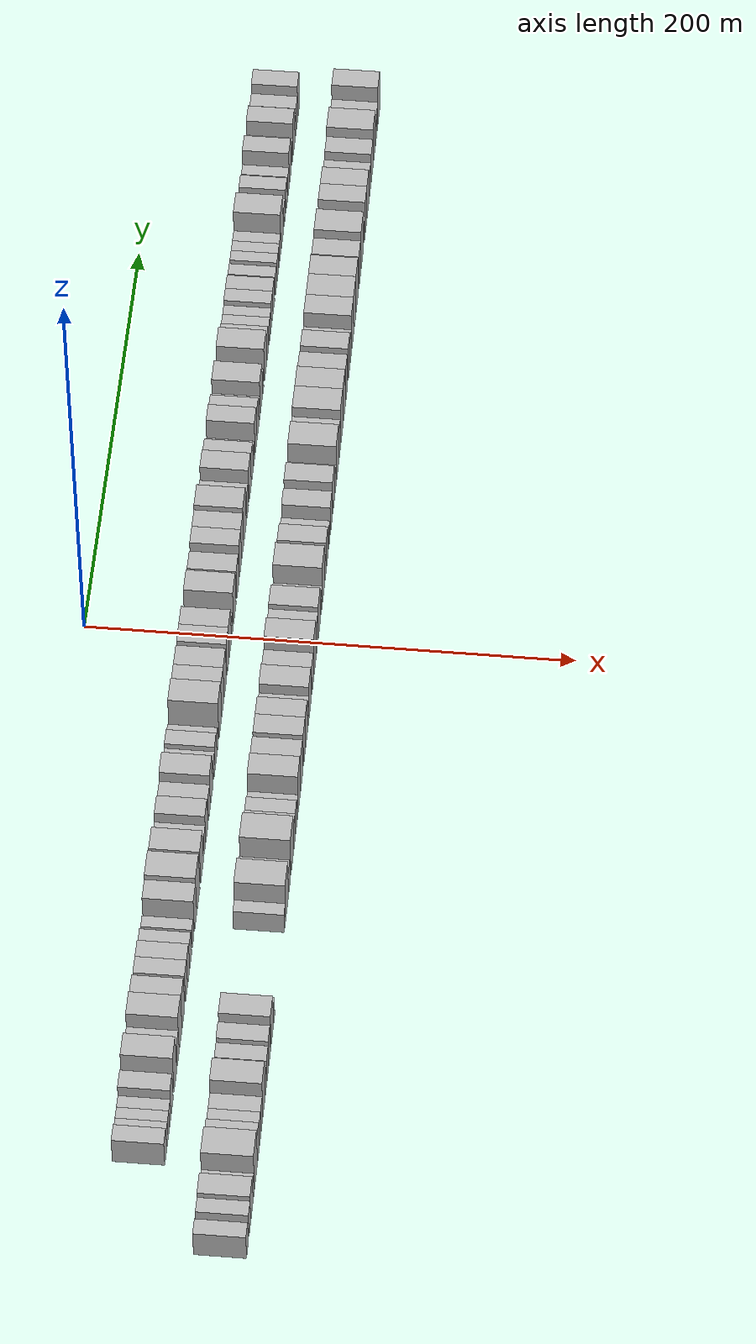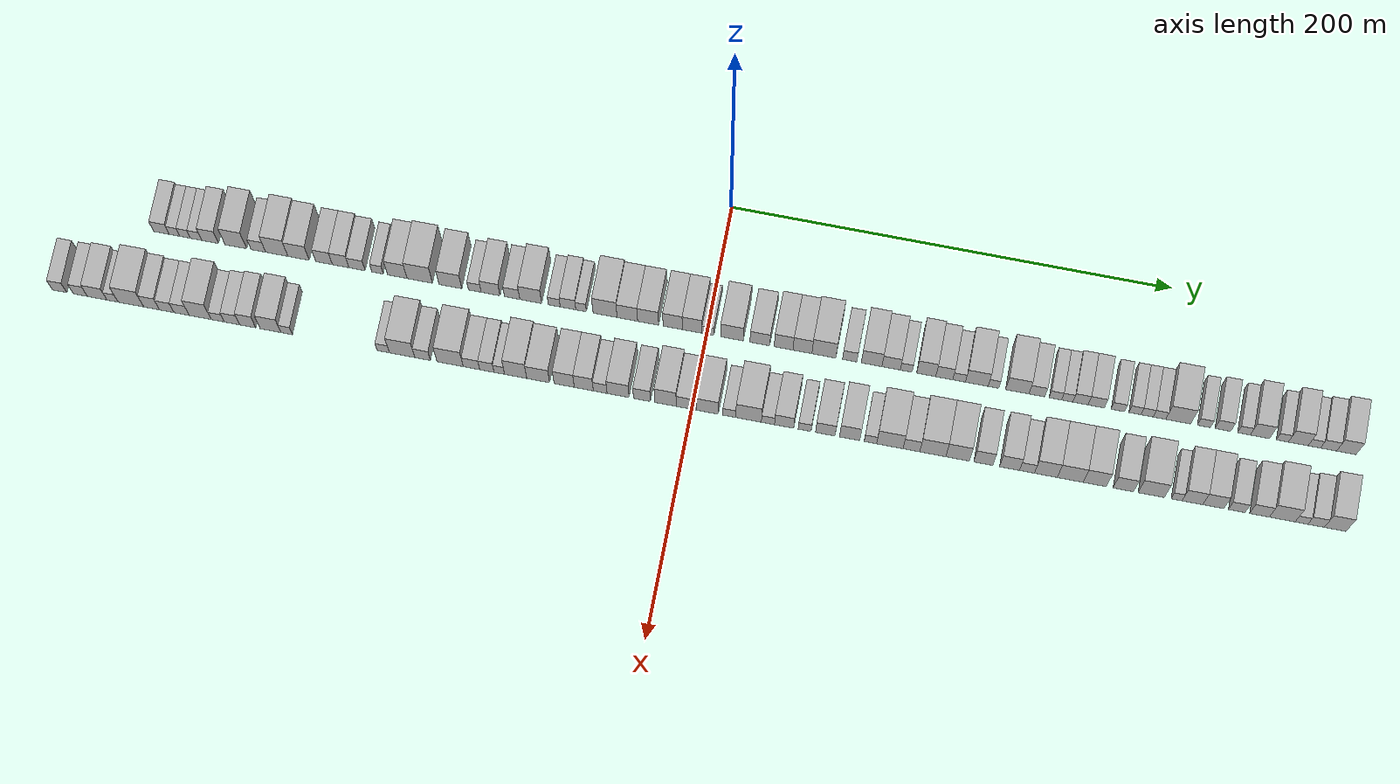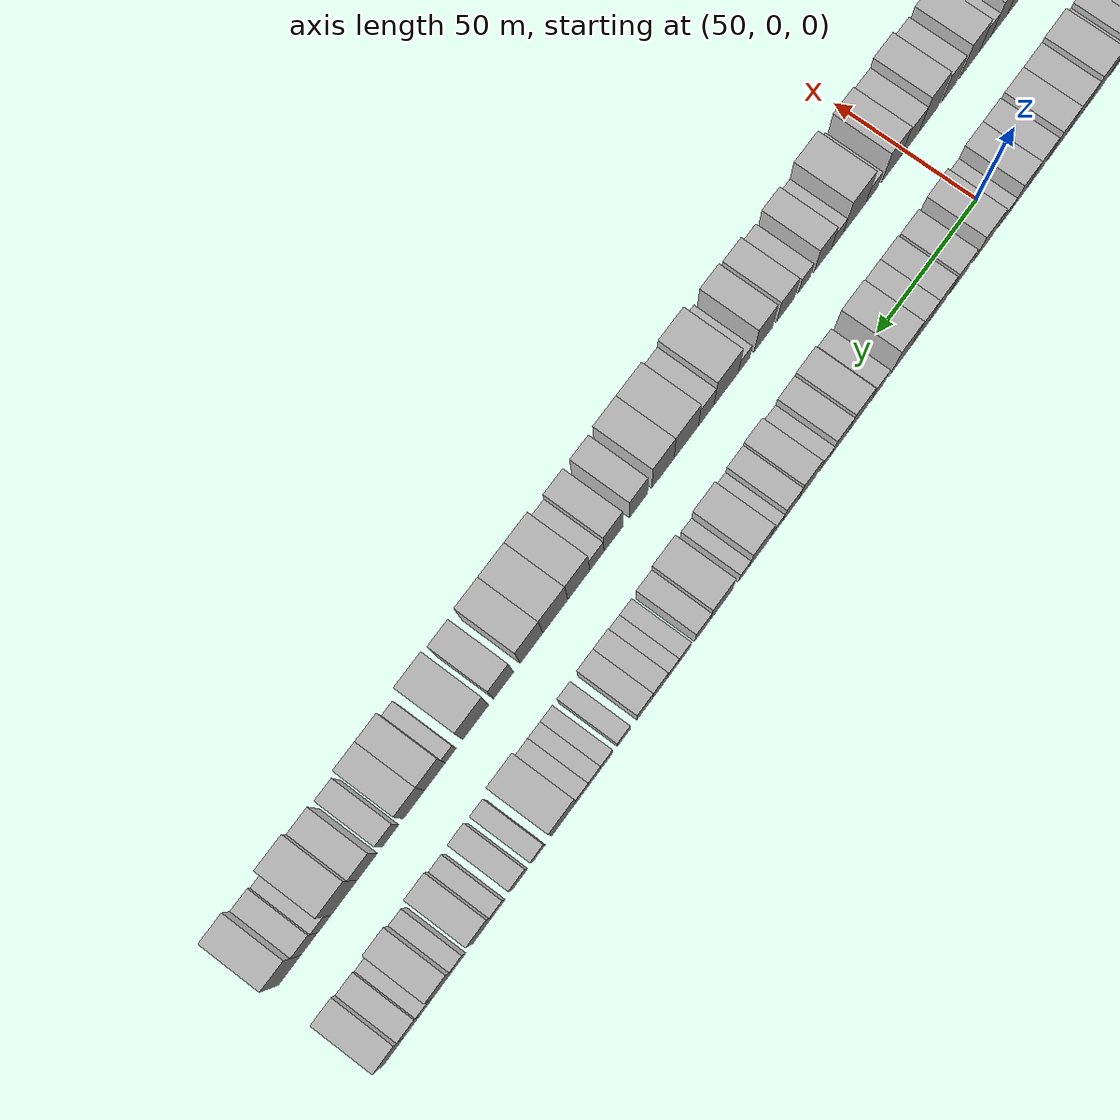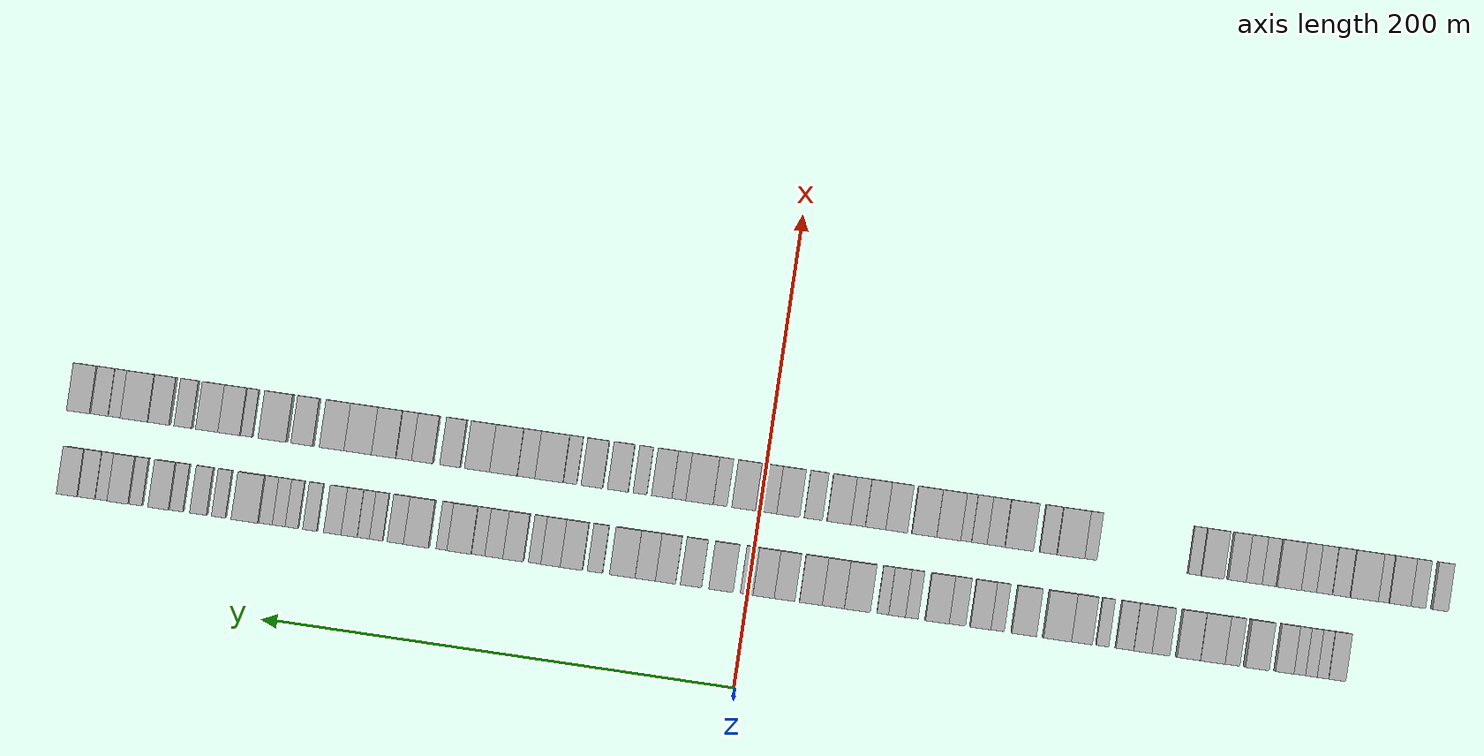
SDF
<sdf version="1.6">
 <world name="default">
  <scene>
   <sky><clouds><speed>12</speed></clouds></sky>
   <ambient>0.4 0.4 0.4 1</ambient>
   <background>0.7 0.7 0.7 1</background>
   <shadows>1</shadows>
  </scene>
  <gravity>0 0 -9.8066</gravity>
  <magnetic_field>6e-06 2.3e-05 -4.2e-05</magnetic_field>
  <physics default="0" name="default_physics" type="ode">
   <ode>
    <solver>
     <type>quick</type>
     <iters>10</iters>
     <sor>1.0</sor>
     <use_dynamic_moi_rescaling>0</use_dynamic_moi_rescaling>
    </solver>
    <constraints>
     <cfm>0</cfm>
     <erp>0.2</erp>
     <contact_max_correcting_vel>100</contact_max_correcting_vel>
     <contact_surface_layer>0.001</contact_surface_layer>
    </constraints>
   </ode>
   <max_step_size>0.004</max_step_size>
   <real_time_factor>1</real_time_factor>
   <real_time_update_rate>250</real_time_update_rate>
  </physics>
  <light name="sun" type="directional">
   <pose>0 0 10 0 0 0</pose>
   <diffuse>0.8 0.8 0.8 1</diffuse>
   <specular>0.2 0.2 0.2 1</specular>
   <attenuation>
    <range>1000</range>
    <constant>0.9</constant>
    <linear>0.01</linear>
    <quadratic>0.001</quadratic>
   </attenuation>
   <direction>-0.5 0.1 -0.9</direction>
  </light>
  <model name="building_1">
   <static>1</static>
   <pose>50.0000 -248.3277 0 0.000000 0.000000 0.000000</pose>
   <link name="link">
    <pose>0 0 7.50 0 0 0</pose>
    <collision name="collision"><geometry><box><size>20.0000 7.1149 15.0000</size></box></geometry></collision>
    <visual name="visual">
     <cast_shadows>0</cast_shadows>
     <geometry><box><size>20.0000 7.1149 15.0000</size></box></geometry>
     <material>
      <script>
       <uri>model://HANNAS_wall/materials/scripts</uri>
       <uri>model://HANNAS_wall/materials/textures</uri>
       <name>vrc/HANNAS_wall</name>
      </script>
     </material>
    </visual>
   </link>
  </model>
  <model name="building_2">
   <static>1</static>
   <pose>50.0000 -242.3634 0 0.000000 0.000000 0.000000</pose>
   <link name="link">
    <pose>0 0 6.00 0 0 0</pose>
    <collision name="collision"><geometry><box><size>20.0000 4.8136 12.0000</size></box></geometry></collision>
    <visual name="visual">
     <cast_shadows>0</cast_shadows>
     <geometry><box><size>20.0000 4.8136 12.0000</size></box></geometry>
     <material>
      <script>
       <uri>model://HANNAS_wall/materials/scripts</uri>
       <uri>model://HANNAS_wall/materials/textures</uri>
       <name>vrc/HANNAS_wall</name>
      </script>
     </material>
    </visual>
   </link>
  </model>
  <model name="building_3">
   <static>1</static>
   <pose>50.0000 -237.5000 0 0.000000 0.000000 0.000000</pose>
   <link name="link">
    <pose>0 0 6.00 0 0 0</pose>
    <collision name="collision"><geometry><box><size>20.0000 4.9132 12.0000</size></box></geometry></collision>
    <visual name="visual">
     <cast_shadows>0</cast_shadows>
     <geometry><box><size>20.0000 4.9132 12.0000</size></box></geometry>
     <material>
      <script>
       <uri>model://HANNAS_wall/materials/scripts</uri>
       <uri>model://HANNAS_wall/materials/textures</uri>
       <name>vrc/HANNAS_wall</name>
      </script>
     </material>
    </visual>
   </link>
  </model>
  <model name="building_4">
   <static>1</static>
   <pose>50.0000 -232.4500 0 0.000000 0.000000 0.000000</pose>
   <link name="link">
    <pose>0 0 6.00 0 0 0</pose>
    <collision name="collision"><geometry><box><size>20.0000 5.1869 12.0000</size></box></geometry></collision>
    <visual name="visual">
     <cast_shadows>0</cast_shadows>
     <geometry><box><size>20.0000 5.1869 12.0000</size></box></geometry>
     <material>
      <script>
       <uri>model://HANNAS_wall/materials/scripts</uri>
       <uri>model://HANNAS_wall/materials/textures</uri>
       <name>vrc/HANNAS_wall</name>
      </script>
     </material>
    </visual>
   </link>
  </model>
  <model name="building_5">
   <static>1</static>
   <pose>50.0000 -226.0046 0 0.000000 0.000000 0.000000</pose>
   <link name="link">
    <pose>0 0 9.00 0 0 0</pose>
    <collision name="collision"><geometry><box><size>20.0000 7.7039 18.0000</size></box></geometry></collision>
    <visual name="visual">
     <cast_shadows>0</cast_shadows>
     <geometry><box><size>20.0000 7.7039 18.0000</size></box></geometry>
     <material>
      <script>
       <uri>model://HANNAS_wall/materials/scripts</uri>
       <uri>model://HANNAS_wall/materials/textures</uri>
       <name>vrc/HANNAS_wall</name>
      </script>
     </material>
    </visual>
   </link>
  </model>
  <model name="building_6">
   <static>1</static>
   <pose>50.0000 -214.1947 0 0.000000 0.000000 0.000000</pose>
   <link name="link">
    <pose>0 0 12.00 0 0 0</pose>
    <collision name="collision"><geometry><box><size>20.0000 9.9158 24.0000</size></box></geometry></collision>
    <visual name="visual">
     <cast_shadows>0</cast_shadows>
     <geometry><box><size>20.0000 9.9158 24.0000</size></box></geometry>
     <material>
      <script>
       <uri>model://HANNAS_wall/materials/scripts</uri>
       <uri>model://HANNAS_wall/materials/textures</uri>
       <name>vrc/HANNAS_wall</name>
      </script>
     </material>
    </visual>
   </link>
  </model>
  <model name="building_7">
   <static>1</static>
   <pose>50.0000 -203.8955 0 0.000000 0.000000 0.000000</pose>
   <link name="link">
    <pose>0 0 7.50 0 0 0</pose>
    <collision name="collision"><geometry><box><size>20.0000 6.6826 15.0000</size></box></geometry></collision>
    <visual name="visual">
     <cast_shadows>0</cast_shadows>
     <geometry><box><size>20.0000 6.6826 15.0000</size></box></geometry>
     <material>
      <script>
       <uri>model://HANNAS_wall/materials/scripts</uri>
       <uri>model://HANNAS_wall/materials/textures</uri>
       <name>vrc/HANNAS_wall</name>
      </script>
     </material>
    </visual>
   </link>
  </model>
  <model name="building_8">
   <static>1</static>
   <pose>50.0000 -195.4504 0 0.000000 0.000000 0.000000</pose>
   <link name="link">
    <pose>0 0 12.00 0 0 0</pose>
    <collision name="collision"><geometry><box><size>20.0000 10.2077 24.0000</size></box></geometry></collision>
    <visual name="visual">
     <cast_shadows>0</cast_shadows>
     <geometry><box><size>20.0000 10.2077 24.0000</size></box></geometry>
     <material>
      <script>
       <uri>model://HANNAS_wall/materials/scripts</uri>
       <uri>model://HANNAS_wall/materials/textures</uri>
       <name>vrc/HANNAS_wall</name>
      </script>
     </material>
    </visual>
   </link>
  </model>
  <model name="building_9">
   <static>1</static>
   <pose>50.0000 -185.4617 0 0.000000 0.000000 0.000000</pose>
   <link name="link">
    <pose>0 0 10.50 0 0 0</pose>
    <collision name="collision"><geometry><box><size>20.0000 9.7698 21.0000</size></box></geometry></collision>
    <visual name="visual">
     <cast_shadows>0</cast_shadows>
     <geometry><box><size>20.0000 9.7698 21.0000</size></box></geometry>
     <material>
      <script>
       <uri>model://HANNAS_wall/materials/scripts</uri>
       <uri>model://HANNAS_wall/materials/textures</uri>
       <name>vrc/HANNAS_wall</name>
      </script>
     </material>
    </visual>
   </link>
  </model>
  <model name="building_10">
   <static>1</static>
   <pose>50.0000 -173.8028 0 0.000000 0.000000 0.000000</pose>
   <link name="link">
    <pose>0 0 9.00 0 0 0</pose>
    <collision name="collision"><geometry><box><size>20.0000 7.5480 18.0000</size></box></geometry></collision>
    <visual name="visual">
     <cast_shadows>0</cast_shadows>
     <geometry><box><size>20.0000 7.5480 18.0000</size></box></geometry>
     <material>
      <script>
       <uri>model://HANNAS_wall/materials/scripts</uri>
       <uri>model://HANNAS_wall/materials/textures</uri>
       <name>vrc/HANNAS_wall</name>
      </script>
     </material>
    </visual>
   </link>
  </model>
  <model name="building_11">
   <static>1</static>
   <pose>50.0000 -166.2367 0 0.000000 0.000000 0.000000</pose>
   <link name="link">
    <pose>0 0 9.00 0 0 0</pose>
    <collision name="collision"><geometry><box><size>20.0000 7.5842 18.0000</size></box></geometry></collision>
    <visual name="visual">
     <cast_shadows>0</cast_shadows>
     <geometry><box><size>20.0000 7.5842 18.0000</size></box></geometry>
     <material>
      <script>
       <uri>model://HANNAS_wall/materials/scripts</uri>
       <uri>model://HANNAS_wall/materials/textures</uri>
       <name>vrc/HANNAS_wall</name>
      </script>
     </material>
    </visual>
   </link>
  </model>
  <model name="building_12">
   <static>1</static>
   <pose>50.0000 -158.7453 0 0.000000 0.000000 0.000000</pose>
   <link name="link">
    <pose>0 0 7.50 0 0 0</pose>
    <collision name="collision"><geometry><box><size>20.0000 7.3986 15.0000</size></box></geometry></collision>
    <visual name="visual">
     <cast_shadows>0</cast_shadows>
     <geometry><box><size>20.0000 7.3986 15.0000</size></box></geometry>
     <material>
      <script>
       <uri>model://HANNAS_wall/materials/scripts</uri>
       <uri>model://HANNAS_wall/materials/textures</uri>
       <name>vrc/HANNAS_wall</name>
      </script>
     </material>
    </visual>
   </link>
  </model>
  <model name="building_13">
   <static>1</static>
   <pose>50.0000 -149.4394 0 0.000000 0.000000 0.000000</pose>
   <link name="link">
    <pose>0 0 6.00 0 0 0</pose>
    <collision name="collision"><geometry><box><size>20.0000 5.2131 12.0000</size></box></geometry></collision>
    <visual name="visual">
     <cast_shadows>0</cast_shadows>
     <geometry><box><size>20.0000 5.2131 12.0000</size></box></geometry>
     <material>
      <script>
       <uri>model://HANNAS_wall/materials/scripts</uri>
       <uri>model://HANNAS_wall/materials/textures</uri>
       <name>vrc/HANNAS_wall</name>
      </script>
     </material>
    </visual>
   </link>
  </model>
  <model name="building_14">
   <static>1</static>
   <pose>50.0000 -140.3880 0 0.000000 0.000000 0.000000</pose>
   <link name="link">
    <pose>0 0 10.50 0 0 0</pose>
    <collision name="collision"><geometry><box><size>20.0000 8.8898 21.0000</size></box></geometry></collision>
    <visual name="visual">
     <cast_shadows>0</cast_shadows>
     <geometry><box><size>20.0000 8.8898 21.0000</size></box></geometry>
     <material>
      <script>
       <uri>model://HANNAS_wall/materials/scripts</uri>
       <uri>model://HANNAS_wall/materials/textures</uri>
       <name>vrc/HANNAS_wall</name>
      </script>
     </material>
    </visual>
   </link>
  </model>
  <model name="building_15">
   <static>1</static>
   <pose>50.0000 -130.1336 0 0.000000 0.000000 0.000000</pose>
   <link name="link">
    <pose>0 0 12.00 0 0 0</pose>
    <collision name="collision"><geometry><box><size>20.0000 11.6189 24.0000</size></box></geometry></collision>
    <visual name="visual">
     <cast_shadows>0</cast_shadows>
     <geometry><box><size>20.0000 11.6189 24.0000</size></box></geometry>
     <material>
      <script>
       <uri>model://HANNAS_wall/materials/scripts</uri>
       <uri>model://HANNAS_wall/materials/textures</uri>
       <name>vrc/HANNAS_wall</name>
      </script>
     </material>
    </visual>
   </link>
  </model>
  <model name="building_16">
   <static>1</static>
   <pose>50.0000 -116.1493 0 0.000000 0.000000 0.000000</pose>
   <link name="link">
    <pose>0 0 10.50 0 0 0</pose>
    <collision name="collision"><geometry><box><size>20.0000 10.3499 21.0000</size></box></geometry></collision>
    <visual name="visual">
     <cast_shadows>0</cast_shadows>
     <geometry><box><size>20.0000 10.3499 21.0000</size></box></geometry>
     <material>
      <script>
       <uri>model://HANNAS_wall/materials/scripts</uri>
       <uri>model://HANNAS_wall/materials/textures</uri>
       <name>vrc/HANNAS_wall</name>
      </script>
     </material>
    </visual>
   </link>
  </model>
  <model name="building_17">
   <static>1</static>
   <pose>50.0000 -105.0805 0 0.000000 0.000000 0.000000</pose>
   <link name="link">
    <pose>0 0 6.00 0 0 0</pose>
    <collision name="collision"><geometry><box><size>20.0000 5.7877 12.0000</size></box></geometry></collision>
    <visual name="visual">
     <cast_shadows>0</cast_shadows>
     <geometry><box><size>20.0000 5.7877 12.0000</size></box></geometry>
     <material>
      <script>
       <uri>model://HANNAS_wall/materials/scripts</uri>
       <uri>model://HANNAS_wall/materials/textures</uri>
       <name>vrc/HANNAS_wall</name>
      </script>
     </material>
    </visual>
   </link>
  </model>
  <model name="building_18">
   <static>1</static>
   <pose>50.0000 -97.8839 0 0.000000 0.000000 0.000000</pose>
   <link name="link">
    <pose>0 0 9.00 0 0 0</pose>
    <collision name="collision"><geometry><box><size>20.0000 8.6054 18.0000</size></box></geometry></collision>
    <visual name="visual">
     <cast_shadows>0</cast_shadows>
     <geometry><box><size>20.0000 8.6054 18.0000</size></box></geometry>
     <material>
      <script>
       <uri>model://HANNAS_wall/materials/scripts</uri>
       <uri>model://HANNAS_wall/materials/textures</uri>
       <name>vrc/HANNAS_wall</name>
      </script>
     </material>
    </visual>
   </link>
  </model>
  <model name="building_19">
   <static>1</static>
   <pose>50.0000 -88.0649 0 0.000000 0.000000 0.000000</pose>
   <link name="link">
    <pose>0 0 7.50 0 0 0</pose>
    <collision name="collision"><geometry><box><size>20.0000 7.0328 15.0000</size></box></geometry></collision>
    <visual name="visual">
     <cast_shadows>0</cast_shadows>
     <geometry><box><size>20.0000 7.0328 15.0000</size></box></geometry>
     <material>
      <script>
       <uri>model://HANNAS_wall/materials/scripts</uri>
       <uri>model://HANNAS_wall/materials/textures</uri>
       <name>vrc/HANNAS_wall</name>
      </script>
     </material>
    </visual>
   </link>
  </model>
  <model name="building_20">
   <static>1</static>
   <pose>50.0000 -79.5889 0 0.000000 0.000000 0.000000</pose>
   <link name="link">
    <pose>0 0 10.50 0 0 0</pose>
    <collision name="collision"><geometry><box><size>20.0000 9.9191 21.0000</size></box></geometry></collision>
    <visual name="visual">
     <cast_shadows>0</cast_shadows>
     <geometry><box><size>20.0000 9.9191 21.0000</size></box></geometry>
     <material>
      <script>
       <uri>model://HANNAS_wall/materials/scripts</uri>
       <uri>model://HANNAS_wall/materials/textures</uri>
       <name>vrc/HANNAS_wall</name>
      </script>
     </material>
    </visual>
   </link>
  </model>
  <model name="building_21">
   <static>1</static>
   <pose>50.0000 -68.9209 0 0.000000 0.000000 0.000000</pose>
   <link name="link">
    <pose>0 0 6.00 0 0 0</pose>
    <collision name="collision"><geometry><box><size>20.0000 5.4170 12.0000</size></box></geometry></collision>
    <visual name="visual">
     <cast_shadows>0</cast_shadows>
     <geometry><box><size>20.0000 5.4170 12.0000</size></box></geometry>
     <material>
      <script>
       <uri>model://HANNAS_wall/materials/scripts</uri>
       <uri>model://HANNAS_wall/materials/textures</uri>
       <name>vrc/HANNAS_wall</name>
      </script>
     </material>
    </visual>
   </link>
  </model>
  <model name="building_22">
   <static>1</static>
   <pose>50.0000 -62.6847 0 0.000000 0.000000 0.000000</pose>
   <link name="link">
    <pose>0 0 7.50 0 0 0</pose>
    <collision name="collision"><geometry><box><size>20.0000 7.0552 15.0000</size></box></geometry></collision>
    <visual name="visual">
     <cast_shadows>0</cast_shadows>
     <geometry><box><size>20.0000 7.0552 15.0000</size></box></geometry>
     <material>
      <script>
       <uri>model://HANNAS_wall/materials/scripts</uri>
       <uri>model://HANNAS_wall/materials/textures</uri>
       <name>vrc/HANNAS_wall</name>
      </script>
     </material>
    </visual>
   </link>
  </model>
  <model name="building_23">
   <static>1</static>
   <pose>50.0000 -56.7431 0 0.000000 0.000000 0.000000</pose>
   <link name="link">
    <pose>0 0 6.00 0 0 0</pose>
    <collision name="collision"><geometry><box><size>20.0000 4.8282 12.0000</size></box></geometry></collision>
    <visual name="visual">
     <cast_shadows>0</cast_shadows>
     <geometry><box><size>20.0000 4.8282 12.0000</size></box></geometry>
     <material>
      <script>
       <uri>model://HANNAS_wall/materials/scripts</uri>
       <uri>model://HANNAS_wall/materials/textures</uri>
       <name>vrc/HANNAS_wall</name>
      </script>
     </material>
    </visual>
   </link>
  </model>
  <model name="building_24">
   <static>1</static>
   <pose>50.0000 -45.8779 0 0.000000 0.000000 0.000000</pose>
   <link name="link">
    <pose>0 0 12.00 0 0 0</pose>
    <collision name="collision"><geometry><box><size>20.0000 10.9021 24.0000</size></box></geometry></collision>
    <visual name="visual">
     <cast_shadows>0</cast_shadows>
     <geometry><box><size>20.0000 10.9021 24.0000</size></box></geometry>
     <material>
      <script>
       <uri>model://HANNAS_wall/materials/scripts</uri>
       <uri>model://HANNAS_wall/materials/textures</uri>
       <name>vrc/HANNAS_wall</name>
      </script>
     </material>
    </visual>
   </link>
  </model>
  <model name="building_25">
   <static>1</static>
   <pose>50.0000 -35.7782 0 0.000000 0.000000 0.000000</pose>
   <link name="link">
    <pose>0 0 10.50 0 0 0</pose>
    <collision name="collision"><geometry><box><size>20.0000 9.2973 21.0000</size></box></geometry></collision>
    <visual name="visual">
     <cast_shadows>0</cast_shadows>
     <geometry><box><size>20.0000 9.2973 21.0000</size></box></geometry>
     <material>
      <script>
       <uri>model://HANNAS_wall/materials/scripts</uri>
       <uri>model://HANNAS_wall/materials/textures</uri>
       <name>vrc/HANNAS_wall</name>
      </script>
     </material>
    </visual>
   </link>
  </model>
  <model name="building_26">
   <static>1</static>
   <pose>50.0000 -26.3639 0 0.000000 0.000000 0.000000</pose>
   <link name="link">
    <pose>0 0 10.50 0 0 0</pose>
    <collision name="collision"><geometry><box><size>20.0000 9.5312 21.0000</size></box></geometry></collision>
    <visual name="visual">
     <cast_shadows>0</cast_shadows>
     <geometry><box><size>20.0000 9.5312 21.0000</size></box></geometry>
     <material>
      <script>
       <uri>model://HANNAS_wall/materials/scripts</uri>
       <uri>model://HANNAS_wall/materials/textures</uri>
       <name>vrc/HANNAS_wall</name>
      </script>
     </material>
    </visual>
   </link>
  </model>
  <model name="building_27">
   <static>1</static>
   <pose>50.0000 -15.2484 0 0.000000 0.000000 0.000000</pose>
   <link name="link">
    <pose>0 0 10.50 0 0 0</pose>
    <collision name="collision"><geometry><box><size>20.0000 8.6997 21.0000</size></box></geometry></collision>
    <visual name="visual">
     <cast_shadows>0</cast_shadows>
     <geometry><box><size>20.0000 8.6997 21.0000</size></box></geometry>
     <material>
      <script>
       <uri>model://HANNAS_wall/materials/scripts</uri>
       <uri>model://HANNAS_wall/materials/textures</uri>
       <name>vrc/HANNAS_wall</name>
      </script>
     </material>
    </visual>
   </link>
  </model>
  <model name="building_28">
   <static>1</static>
   <pose>50.0000 -6.4340 0 0.000000 0.000000 0.000000</pose>
   <link name="link">
    <pose>0 0 10.50 0 0 0</pose>
    <collision name="collision"><geometry><box><size>20.0000 8.9290 21.0000</size></box></geometry></collision>
    <visual name="visual">
     <cast_shadows>0</cast_shadows>
     <geometry><box><size>20.0000 8.9290 21.0000</size></box></geometry>
     <material>
      <script>
       <uri>model://HANNAS_wall/materials/scripts</uri>
       <uri>model://HANNAS_wall/materials/textures</uri>
       <name>vrc/HANNAS_wall</name>
      </script>
     </material>
    </visual>
   </link>
  </model>
  <model name="building_29">
   <static>1</static>
   <pose>50.0000 0.7145 0 0.000000 0.000000 0.000000</pose>
   <link name="link">
    <pose>0 0 6.00 0 0 0</pose>
    <collision name="collision"><geometry><box><size>20.0000 5.3681 12.0000</size></box></geometry></collision>
    <visual name="visual">
     <cast_shadows>0</cast_shadows>
     <geometry><box><size>20.0000 5.3681 12.0000</size></box></geometry>
     <material>
      <script>
       <uri>model://HANNAS_wall/materials/scripts</uri>
       <uri>model://HANNAS_wall/materials/textures</uri>
       <name>vrc/HANNAS_wall</name>
      </script>
     </material>
    </visual>
   </link>
  </model>
  <model name="building_30">
   <static>1</static>
   <pose>50.0000 11.5483 0 0.000000 0.000000 0.000000</pose>
   <link name="link">
    <pose>0 0 10.50 0 0 0</pose>
    <collision name="collision"><geometry><box><size>20.0000 10.2995 21.0000</size></box></geometry></collision>
    <visual name="visual">
     <cast_shadows>0</cast_shadows>
     <geometry><box><size>20.0000 10.2995 21.0000</size></box></geometry>
     <material>
      <script>
       <uri>model://HANNAS_wall/materials/scripts</uri>
       <uri>model://HANNAS_wall/materials/textures</uri>
       <name>vrc/HANNAS_wall</name>
      </script>
     </material>
    </visual>
   </link>
  </model>
  <model name="building_31">
   <static>1</static>
   <pose>50.0000 24.1749 0 0.000000 0.000000 0.000000</pose>
   <link name="link">
    <pose>0 0 9.00 0 0 0</pose>
    <collision name="collision"><geometry><box><size>20.0000 8.9537 18.0000</size></box></geometry></collision>
    <visual name="visual">
     <cast_shadows>0</cast_shadows>
     <geometry><box><size>20.0000 8.9537 18.0000</size></box></geometry>
     <material>
      <script>
       <uri>model://HANNAS_wall/materials/scripts</uri>
       <uri>model://HANNAS_wall/materials/textures</uri>
       <name>vrc/HANNAS_wall</name>
      </script>
     </material>
    </visual>
   </link>
  </model>
  <model name="building_32">
   <static>1</static>
   <pose>50.0000 34.8956 0 0.000000 0.000000 0.000000</pose>
   <link name="link">
    <pose>0 0 10.50 0 0 0</pose>
    <collision name="collision"><geometry><box><size>20.0000 8.4877 21.0000</size></box></geometry></collision>
    <visual name="visual">
     <cast_shadows>0</cast_shadows>
     <geometry><box><size>20.0000 8.4877 21.0000</size></box></geometry>
     <material>
      <script>
       <uri>model://HANNAS_wall/materials/scripts</uri>
       <uri>model://HANNAS_wall/materials/textures</uri>
       <name>vrc/HANNAS_wall</name>
      </script>
     </material>
    </visual>
   </link>
  </model>
  <model name="building_33">
   <static>1</static>
   <pose>50.0000 43.4149 0 0.000000 0.000000 0.000000</pose>
   <link name="link">
    <pose>0 0 10.50 0 0 0</pose>
    <collision name="collision"><geometry><box><size>20.0000 8.5508 21.0000</size></box></geometry></collision>
    <visual name="visual">
     <cast_shadows>0</cast_shadows>
     <geometry><box><size>20.0000 8.5508 21.0000</size></box></geometry>
     <material>
      <script>
       <uri>model://HANNAS_wall/materials/scripts</uri>
       <uri>model://HANNAS_wall/materials/textures</uri>
       <name>vrc/HANNAS_wall</name>
      </script>
     </material>
    </visual>
   </link>
  </model>
  <model name="building_34">
   <static>1</static>
   <pose>50.0000 53.0832 0 0.000000 0.000000 0.000000</pose>
   <link name="link">
    <pose>0 0 12.00 0 0 0</pose>
    <collision name="collision"><geometry><box><size>20.0000 10.7860 24.0000</size></box></geometry></collision>
    <visual name="visual">
     <cast_shadows>0</cast_shadows>
     <geometry><box><size>20.0000 10.7860 24.0000</size></box></geometry>
     <material>
      <script>
       <uri>model://HANNAS_wall/materials/scripts</uri>
       <uri>model://HANNAS_wall/materials/textures</uri>
       <name>vrc/HANNAS_wall</name>
      </script>
     </material>
    </visual>
   </link>
  </model>
  <model name="building_35">
   <static>1</static>
   <pose>50.0000 64.6992 0 0.000000 0.000000 0.000000</pose>
   <link name="link">
    <pose>0 0 7.50 0 0 0</pose>
    <collision name="collision"><geometry><box><size>20.0000 6.4458 15.0000</size></box></geometry></collision>
    <visual name="visual">
     <cast_shadows>0</cast_shadows>
     <geometry><box><size>20.0000 6.4458 15.0000</size></box></geometry>
     <material>
      <script>
       <uri>model://HANNAS_wall/materials/scripts</uri>
       <uri>model://HANNAS_wall/materials/textures</uri>
       <name>vrc/HANNAS_wall</name>
      </script>
     </material>
    </visual>
   </link>
  </model>
  <model name="building_36">
   <static>1</static>
   <pose>50.0000 74.5765 0 0.000000 0.000000 0.000000</pose>
   <link name="link">
    <pose>0 0 10.50 0 0 0</pose>
    <collision name="collision"><geometry><box><size>20.0000 9.3089 21.0000</size></box></geometry></collision>
    <visual name="visual">
     <cast_shadows>0</cast_shadows>
     <geometry><box><size>20.0000 9.3089 21.0000</size></box></geometry>
     <material>
      <script>
       <uri>model://HANNAS_wall/materials/scripts</uri>
       <uri>model://HANNAS_wall/materials/textures</uri>
       <name>vrc/HANNAS_wall</name>
      </script>
     </material>
    </visual>
   </link>
  </model>
  <model name="building_37">
   <static>1</static>
   <pose>50.0000 83.3503 0 0.000000 0.000000 0.000000</pose>
   <link name="link">
    <pose>0 0 9.00 0 0 0</pose>
    <collision name="collision"><geometry><box><size>20.0000 8.2386 18.0000</size></box></geometry></collision>
    <visual name="visual">
     <cast_shadows>0</cast_shadows>
     <geometry><box><size>20.0000 8.2386 18.0000</size></box></geometry>
     <material>
      <script>
       <uri>model://HANNAS_wall/materials/scripts</uri>
       <uri>model://HANNAS_wall/materials/textures</uri>
       <name>vrc/HANNAS_wall</name>
      </script>
     </material>
    </visual>
   </link>
  </model>
  <model name="building_38">
   <static>1</static>
   <pose>50.0000 90.1507 0 0.000000 0.000000 0.000000</pose>
   <link name="link">
    <pose>0 0 6.00 0 0 0</pose>
    <collision name="collision"><geometry><box><size>20.0000 5.3623 12.0000</size></box></geometry></collision>
    <visual name="visual">
     <cast_shadows>0</cast_shadows>
     <geometry><box><size>20.0000 5.3623 12.0000</size></box></geometry>
     <material>
      <script>
       <uri>model://HANNAS_wall/materials/scripts</uri>
       <uri>model://HANNAS_wall/materials/textures</uri>
       <name>vrc/HANNAS_wall</name>
      </script>
     </material>
    </visual>
   </link>
  </model>
  <model name="building_39">
   <static>1</static>
   <pose>50.0000 99.1289 0 0.000000 0.000000 0.000000</pose>
   <link name="link">
    <pose>0 0 10.50 0 0 0</pose>
    <collision name="collision"><geometry><box><size>20.0000 8.5942 21.0000</size></box></geometry></collision>
    <visual name="visual">
     <cast_shadows>0</cast_shadows>
     <geometry><box><size>20.0000 8.5942 21.0000</size></box></geometry>
     <material>
      <script>
       <uri>model://HANNAS_wall/materials/scripts</uri>
       <uri>model://HANNAS_wall/materials/textures</uri>
       <name>vrc/HANNAS_wall</name>
      </script>
     </material>
    </visual>
   </link>
  </model>
  <model name="building_40">
   <static>1</static>
   <pose>50.0000 107.2509 0 0.000000 0.000000 0.000000</pose>
   <link name="link">
    <pose>0 0 9.00 0 0 0</pose>
    <collision name="collision"><geometry><box><size>20.0000 7.6497 18.0000</size></box></geometry></collision>
    <visual name="visual">
     <cast_shadows>0</cast_shadows>
     <geometry><box><size>20.0000 7.6497 18.0000</size></box></geometry>
     <material>
      <script>
       <uri>model://HANNAS_wall/materials/scripts</uri>
       <uri>model://HANNAS_wall/materials/textures</uri>
       <name>vrc/HANNAS_wall</name>
      </script>
     </material>
    </visual>
   </link>
  </model>
  <model name="building_41">
   <static>1</static>
   <pose>50.0000 113.9115 0 0.000000 0.000000 0.000000</pose>
   <link name="link">
    <pose>0 0 6.00 0 0 0</pose>
    <collision name="collision"><geometry><box><size>20.0000 5.6714 12.0000</size></box></geometry></collision>
    <visual name="visual">
     <cast_shadows>0</cast_shadows>
     <geometry><box><size>20.0000 5.6714 12.0000</size></box></geometry>
     <material>
      <script>
       <uri>model://HANNAS_wall/materials/scripts</uri>
       <uri>model://HANNAS_wall/materials/textures</uri>
       <name>vrc/HANNAS_wall</name>
      </script>
     </material>
    </visual>
   </link>
  </model>
  <model name="building_42">
   <static>1</static>
   <pose>50.0000 121.8345 0 0.000000 0.000000 0.000000</pose>
   <link name="link">
    <pose>0 0 10.50 0 0 0</pose>
    <collision name="collision"><geometry><box><size>20.0000 10.1746 21.0000</size></box></geometry></collision>
    <visual name="visual">
     <cast_shadows>0</cast_shadows>
     <geometry><box><size>20.0000 10.1746 21.0000</size></box></geometry>
     <material>
      <script>
       <uri>model://HANNAS_wall/materials/scripts</uri>
       <uri>model://HANNAS_wall/materials/textures</uri>
       <name>vrc/HANNAS_wall</name>
      </script>
     </material>
    </visual>
   </link>
  </model>
  <model name="building_43">
   <static>1</static>
   <pose>50.0000 129.3397 0 0.000000 0.000000 0.000000</pose>
   <link name="link">
    <pose>0 0 6.00 0 0 0</pose>
    <collision name="collision"><geometry><box><size>20.0000 4.8359 12.0000</size></box></geometry></collision>
    <visual name="visual">
     <cast_shadows>0</cast_shadows>
     <geometry><box><size>20.0000 4.8359 12.0000</size></box></geometry>
     <material>
      <script>
       <uri>model://HANNAS_wall/materials/scripts</uri>
       <uri>model://HANNAS_wall/materials/textures</uri>
       <name>vrc/HANNAS_wall</name>
      </script>
     </material>
    </visual>
   </link>
  </model>
  <model name="building_44">
   <static>1</static>
   <pose>50.0000 139.9928 0 0.000000 0.000000 0.000000</pose>
   <link name="link">
    <pose>0 0 10.50 0 0 0</pose>
    <collision name="collision"><geometry><box><size>20.0000 10.4704 21.0000</size></box></geometry></collision>
    <visual name="visual">
     <cast_shadows>0</cast_shadows>
     <geometry><box><size>20.0000 10.4704 21.0000</size></box></geometry>
     <material>
      <script>
       <uri>model://HANNAS_wall/materials/scripts</uri>
       <uri>model://HANNAS_wall/materials/textures</uri>
       <name>vrc/HANNAS_wall</name>
      </script>
     </material>
    </visual>
   </link>
  </model>
  <model name="building_45">
   <static>1</static>
   <pose>50.0000 148.7830 0 0.000000 0.000000 0.000000</pose>
   <link name="link">
    <pose>0 0 7.50 0 0 0</pose>
    <collision name="collision"><geometry><box><size>20.0000 7.1100 15.0000</size></box></geometry></collision>
    <visual name="visual">
     <cast_shadows>0</cast_shadows>
     <geometry><box><size>20.0000 7.1100 15.0000</size></box></geometry>
     <material>
      <script>
       <uri>model://HANNAS_wall/materials/scripts</uri>
       <uri>model://HANNAS_wall/materials/textures</uri>
       <name>vrc/HANNAS_wall</name>
      </script>
     </material>
    </visual>
   </link>
  </model>
  <model name="building_46">
   <static>1</static>
   <pose>50.0000 157.1100 0 0.000000 0.000000 0.000000</pose>
   <link name="link">
    <pose>0 0 6.00 0 0 0</pose>
    <collision name="collision"><geometry><box><size>20.0000 5.5440 12.0000</size></box></geometry></collision>
    <visual name="visual">
     <cast_shadows>0</cast_shadows>
     <geometry><box><size>20.0000 5.5440 12.0000</size></box></geometry>
     <material>
      <script>
       <uri>model://HANNAS_wall/materials/scripts</uri>
       <uri>model://HANNAS_wall/materials/textures</uri>
       <name>vrc/HANNAS_wall</name>
      </script>
     </material>
    </visual>
   </link>
  </model>
  <model name="building_47">
   <static>1</static>
   <pose>50.0000 162.4199 0 0.000000 0.000000 0.000000</pose>
   <link name="link">
    <pose>0 0 6.00 0 0 0</pose>
    <collision name="collision"><geometry><box><size>20.0000 5.0758 12.0000</size></box></geometry></collision>
    <visual name="visual">
     <cast_shadows>0</cast_shadows>
     <geometry><box><size>20.0000 5.0758 12.0000</size></box></geometry>
     <material>
      <script>
       <uri>model://HANNAS_wall/materials/scripts</uri>
       <uri>model://HANNAS_wall/materials/textures</uri>
       <name>vrc/HANNAS_wall</name>
      </script>
     </material>
    </visual>
   </link>
  </model>
  <model name="building_48">
   <static>1</static>
   <pose>50.0000 168.3564 0 0.000000 0.000000 0.000000</pose>
   <link name="link">
    <pose>0 0 7.50 0 0 0</pose>
    <collision name="collision"><geometry><box><size>20.0000 6.7971 15.0000</size></box></geometry></collision>
    <visual name="visual">
     <cast_shadows>0</cast_shadows>
     <geometry><box><size>20.0000 6.7971 15.0000</size></box></geometry>
     <material>
      <script>
       <uri>model://HANNAS_wall/materials/scripts</uri>
       <uri>model://HANNAS_wall/materials/textures</uri>
       <name>vrc/HANNAS_wall</name>
      </script>
     </material>
    </visual>
   </link>
  </model>
  <model name="building_49">
   <static>1</static>
   <pose>50.0000 175.4226 0 0.000000 0.000000 0.000000</pose>
   <link name="link">
    <pose>0 0 7.50 0 0 0</pose>
    <collision name="collision"><geometry><box><size>20.0000 7.3352 15.0000</size></box></geometry></collision>
    <visual name="visual">
     <cast_shadows>0</cast_shadows>
     <geometry><box><size>20.0000 7.3352 15.0000</size></box></geometry>
     <material>
      <script>
       <uri>model://HANNAS_wall/materials/scripts</uri>
       <uri>model://HANNAS_wall/materials/textures</uri>
       <name>vrc/HANNAS_wall</name>
      </script>
     </material>
    </visual>
   </link>
  </model>
  <model name="building_50">
   <static>1</static>
   <pose>50.0000 185.0558 0 0.000000 0.000000 0.000000</pose>
   <link name="link">
    <pose>0 0 6.00 0 0 0</pose>
    <collision name="collision"><geometry><box><size>20.0000 5.9312 12.0000</size></box></geometry></collision>
    <visual name="visual">
     <cast_shadows>0</cast_shadows>
     <geometry><box><size>20.0000 5.9312 12.0000</size></box></geometry>
     <material>
      <script>
       <uri>model://HANNAS_wall/materials/scripts</uri>
       <uri>model://HANNAS_wall/materials/textures</uri>
       <name>vrc/HANNAS_wall</name>
      </script>
     </material>
    </visual>
   </link>
  </model>
  <model name="building_51">
   <static>1</static>
   <pose>50.0000 192.7203 0 0.000000 0.000000 0.000000</pose>
   <link name="link">
    <pose>0 0 6.00 0 0 0</pose>
    <collision name="collision"><geometry><box><size>20.0000 5.3978 12.0000</size></box></geometry></collision>
    <visual name="visual">
     <cast_shadows>0</cast_shadows>
     <geometry><box><size>20.0000 5.3978 12.0000</size></box></geometry>
     <material>
      <script>
       <uri>model://HANNAS_wall/materials/scripts</uri>
       <uri>model://HANNAS_wall/materials/textures</uri>
       <name>vrc/HANNAS_wall</name>
      </script>
     </material>
    </visual>
   </link>
  </model>
  <model name="building_52">
   <static>1</static>
   <pose>50.0000 198.1457 0 0.000000 0.000000 0.000000</pose>
   <link name="link">
    <pose>0 0 6.00 0 0 0</pose>
    <collision name="collision"><geometry><box><size>20.0000 5.4532 12.0000</size></box></geometry></collision>
    <visual name="visual">
     <cast_shadows>0</cast_shadows>
     <geometry><box><size>20.0000 5.4532 12.0000</size></box></geometry>
     <material>
      <script>
       <uri>model://HANNAS_wall/materials/scripts</uri>
       <uri>model://HANNAS_wall/materials/textures</uri>
       <name>vrc/HANNAS_wall</name>
      </script>
     </material>
    </visual>
   </link>
  </model>
  <model name="building_53">
   <static>1</static>
   <pose>50.0000 203.6819 0 0.000000 0.000000 0.000000</pose>
   <link name="link">
    <pose>0 0 6.00 0 0 0</pose>
    <collision name="collision"><geometry><box><size>20.0000 5.6191 12.0000</size></box></geometry></collision>
    <visual name="visual">
     <cast_shadows>0</cast_shadows>
     <geometry><box><size>20.0000 5.6191 12.0000</size></box></geometry>
     <material>
      <script>
       <uri>model://HANNAS_wall/materials/scripts</uri>
       <uri>model://HANNAS_wall/materials/textures</uri>
       <name>vrc/HANNAS_wall</name>
      </script>
     </material>
    </visual>
   </link>
  </model>
  <model name="building_54">
   <static>1</static>
   <pose>50.0000 212.0614 0 0.000000 0.000000 0.000000</pose>
   <link name="link">
    <pose>0 0 12.00 0 0 0</pose>
    <collision name="collision"><geometry><box><size>20.0000 11.1399 24.0000</size></box></geometry></collision>
    <visual name="visual">
     <cast_shadows>0</cast_shadows>
     <geometry><box><size>20.0000 11.1399 24.0000</size></box></geometry>
     <material>
      <script>
       <uri>model://HANNAS_wall/materials/scripts</uri>
       <uri>model://HANNAS_wall/materials/textures</uri>
       <name>vrc/HANNAS_wall</name>
      </script>
     </material>
    </visual>
   </link>
  </model>
  <model name="building_55">
   <static>1</static>
   <pose>50.0000 223.5613 0 0.000000 0.000000 0.000000</pose>
   <link name="link">
    <pose>0 0 6.00 0 0 0</pose>
    <collision name="collision"><geometry><box><size>20.0000 5.8598 12.0000</size></box></geometry></collision>
    <visual name="visual">
     <cast_shadows>0</cast_shadows>
     <geometry><box><size>20.0000 5.8598 12.0000</size></box></geometry>
     <material>
      <script>
       <uri>model://HANNAS_wall/materials/scripts</uri>
       <uri>model://HANNAS_wall/materials/textures</uri>
       <name>vrc/HANNAS_wall</name>
      </script>
     </material>
    </visual>
   </link>
  </model>
  <model name="building_56">
   <static>1</static>
   <pose>50.0000 232.0215 0 0.000000 0.000000 0.000000</pose>
   <link name="link">
    <pose>0 0 7.50 0 0 0</pose>
    <collision name="collision"><geometry><box><size>20.0000 7.0606 15.0000</size></box></geometry></collision>
    <visual name="visual">
     <cast_shadows>0</cast_shadows>
     <geometry><box><size>20.0000 7.0606 15.0000</size></box></geometry>
     <material>
      <script>
       <uri>model://HANNAS_wall/materials/scripts</uri>
       <uri>model://HANNAS_wall/materials/textures</uri>
       <name>vrc/HANNAS_wall</name>
      </script>
     </material>
    </visual>
   </link>
  </model>
  <model name="building_57">
   <static>1</static>
   <pose>50.0000 241.3652 0 0.000000 0.000000 0.000000</pose>
   <link name="link">
    <pose>0 0 6.00 0 0 0</pose>
    <collision name="collision"><geometry><box><size>20.0000 5.6268 12.0000</size></box></geometry></collision>
    <visual name="visual">
     <cast_shadows>0</cast_shadows>
     <geometry><box><size>20.0000 5.6268 12.0000</size></box></geometry>
     <material>
      <script>
       <uri>model://HANNAS_wall/materials/scripts</uri>
       <uri>model://HANNAS_wall/materials/textures</uri>
       <name>vrc/HANNAS_wall</name>
      </script>
     </material>
    </visual>
   </link>
  </model>
  <model name="building_58">
   <static>1</static>
   <pose>50.0000 248.5094 0 0.000000 0.000000 0.000000</pose>
   <link name="link">
    <pose>0 0 10.50 0 0 0</pose>
    <collision name="collision"><geometry><box><size>20.0000 8.6616 21.0000</size></box></geometry></collision>
    <visual name="visual">
     <cast_shadows>0</cast_shadows>
     <geometry><box><size>20.0000 8.6616 21.0000</size></box></geometry>
     <material>
      <script>
       <uri>model://HANNAS_wall/materials/scripts</uri>
       <uri>model://HANNAS_wall/materials/textures</uri>
       <name>vrc/HANNAS_wall</name>
      </script>
     </material>
    </visual>
   </link>
  </model>
  <model name="building_59">
   <static>1</static>
   <pose>50.0000 258.5315 0 0.000000 0.000000 0.000000</pose>
   <link name="link">
    <pose>0 0 6.00 0 0 0</pose>
    <collision name="collision"><geometry><box><size>20.0000 5.3826 12.0000</size></box></geometry></collision>
    <visual name="visual">
     <cast_shadows>0</cast_shadows>
     <geometry><box><size>20.0000 5.3826 12.0000</size></box></geometry>
     <material>
      <script>
       <uri>model://HANNAS_wall/materials/scripts</uri>
       <uri>model://HANNAS_wall/materials/textures</uri>
       <name>vrc/HANNAS_wall</name>
      </script>
     </material>
    </visual>
   </link>
  </model>
  <model name="building_60">
   <static>1</static>
   <pose>50.0000 265.6343 0 0.000000 0.000000 0.000000</pose>
   <link name="link">
    <pose>0 0 10.50 0 0 0</pose>
    <collision name="collision"><geometry><box><size>20.0000 8.8230 21.0000</size></box></geometry></collision>
    <visual name="visual">
     <cast_shadows>0</cast_shadows>
     <geometry><box><size>20.0000 8.8230 21.0000</size></box></geometry>
     <material>
      <script>
       <uri>model://HANNAS_wall/materials/scripts</uri>
       <uri>model://HANNAS_wall/materials/textures</uri>
       <name>vrc/HANNAS_wall</name>
      </script>
     </material>
    </visual>
   </link>
  </model>
  <model name="building_61">
   <static>1</static>
   <pose>50.0000 272.7663 0 0.000000 0.000000 0.000000</pose>
   <link name="link">
    <pose>0 0 6.00 0 0 0</pose>
    <collision name="collision"><geometry><box><size>20.0000 5.4410 12.0000</size></box></geometry></collision>
    <visual name="visual">
     <cast_shadows>0</cast_shadows>
     <geometry><box><size>20.0000 5.4410 12.0000</size></box></geometry>
     <material>
      <script>
       <uri>model://HANNAS_wall/materials/scripts</uri>
       <uri>model://HANNAS_wall/materials/textures</uri>
       <name>vrc/HANNAS_wall</name>
      </script>
     </material>
    </visual>
   </link>
  </model>
  <model name="building_62">
   <static>1</static>
   <pose>50.0000 279.0980 0 0.000000 0.000000 0.000000</pose>
   <link name="link">
    <pose>0 0 7.50 0 0 0</pose>
    <collision name="collision"><geometry><box><size>20.0000 7.2223 15.0000</size></box></geometry></collision>
    <visual name="visual">
     <cast_shadows>0</cast_shadows>
     <geometry><box><size>20.0000 7.2223 15.0000</size></box></geometry>
     <material>
      <script>
       <uri>model://HANNAS_wall/materials/scripts</uri>
       <uri>model://HANNAS_wall/materials/textures</uri>
       <name>vrc/HANNAS_wall</name>
      </script>
     </material>
    </visual>
   </link>
  </model>
  <model name="building_63">
   <static>1</static>
   <pose>50.0000 287.0207 0 0.000000 0.000000 0.000000</pose>
   <link name="link">
    <pose>0 0 10.50 0 0 0</pose>
    <collision name="collision"><geometry><box><size>20.0000 8.6232 21.0000</size></box></geometry></collision>
    <visual name="visual">
     <cast_shadows>0</cast_shadows>
     <geometry><box><size>20.0000 8.6232 21.0000</size></box></geometry>
     <material>
      <script>
       <uri>model://HANNAS_wall/materials/scripts</uri>
       <uri>model://HANNAS_wall/materials/textures</uri>
       <name>vrc/HANNAS_wall</name>
      </script>
     </material>
    </visual>
   </link>
  </model>
  <model name="building_64">
   <static>1</static>
   <pose>85.0000 -286.7064 0 0.000000 0.000000 0.000000</pose>
   <link name="link">
    <pose>0 0 7.50 0 0 0</pose>
    <collision name="collision"><geometry><box><size>20.0000 6.5872 15.0000</size></box></geometry></collision>
    <visual name="visual">
     <cast_shadows>0</cast_shadows>
     <geometry><box><size>20.0000 6.5872 15.0000</size></box></geometry>
     <material>
      <script>
       <uri>model://HANNAS_wall/materials/scripts</uri>
       <uri>model://HANNAS_wall/materials/textures</uri>
       <name>vrc/HANNAS_wall</name>
      </script>
     </material>
    </visual>
   </link>
  </model>
  <model name="building_65">
   <static>1</static>
   <pose>85.0000 -277.2148 0 0.000000 0.000000 0.000000</pose>
   <link name="link">
    <pose>0 0 7.50 0 0 0</pose>
    <collision name="collision"><geometry><box><size>20.0000 6.3959 15.0000</size></box></geometry></collision>
    <visual name="visual">
     <cast_shadows>0</cast_shadows>
     <geometry><box><size>20.0000 6.3959 15.0000</size></box></geometry>
     <material>
      <script>
       <uri>model://HANNAS_wall/materials/scripts</uri>
       <uri>model://HANNAS_wall/materials/textures</uri>
       <name>vrc/HANNAS_wall</name>
      </script>
     </material>
    </visual>
   </link>
  </model>
  <model name="building_66">
   <static>1</static>
   <pose>85.0000 -269.5321 0 0.000000 0.000000 0.000000</pose>
   <link name="link">
    <pose>0 0 9.00 0 0 0</pose>
    <collision name="collision"><geometry><box><size>20.0000 8.9697 18.0000</size></box></geometry></collision>
    <visual name="visual">
     <cast_shadows>0</cast_shadows>
     <geometry><box><size>20.0000 8.9697 18.0000</size></box></geometry>
     <material>
      <script>
       <uri>model://HANNAS_wall/materials/scripts</uri>
       <uri>model://HANNAS_wall/materials/textures</uri>
       <name>vrc/HANNAS_wall</name>
      </script>
     </material>
    </visual>
   </link>
  </model>
  <model name="building_67">
   <static>1</static>
   <pose>85.0000 -262.4926 0 0.000000 0.000000 0.000000</pose>
   <link name="link">
    <pose>0 0 6.00 0 0 0</pose>
    <collision name="collision"><geometry><box><size>20.0000 5.1092 12.0000</size></box></geometry></collision>
    <visual name="visual">
     <cast_shadows>0</cast_shadows>
     <geometry><box><size>20.0000 5.1092 12.0000</size></box></geometry>
     <material>
      <script>
       <uri>model://HANNAS_wall/materials/scripts</uri>
       <uri>model://HANNAS_wall/materials/textures</uri>
       <name>vrc/HANNAS_wall</name>
      </script>
     </material>
    </visual>
   </link>
  </model>
  <model name="building_68">
   <static>1</static>
   <pose>85.0000 -254.1048 0 0.000000 0.000000 0.000000</pose>
   <link name="link">
    <pose>0 0 12.00 0 0 0</pose>
    <collision name="collision"><geometry><box><size>20.0000 11.6662 24.0000</size></box></geometry></collision>
    <visual name="visual">
     <cast_shadows>0</cast_shadows>
     <geometry><box><size>20.0000 11.6662 24.0000</size></box></geometry>
     <material>
      <script>
       <uri>model://HANNAS_wall/materials/scripts</uri>
       <uri>model://HANNAS_wall/materials/textures</uri>
       <name>vrc/HANNAS_wall</name>
      </script>
     </material>
    </visual>
   </link>
  </model>
  <model name="building_69">
   <static>1</static>
   <pose>85.0000 -244.6632 0 0.000000 0.000000 0.000000</pose>
   <link name="link">
    <pose>0 0 9.00 0 0 0</pose>
    <collision name="collision"><geometry><box><size>20.0000 7.2171 18.0000</size></box></geometry></collision>
    <visual name="visual">
     <cast_shadows>0</cast_shadows>
     <geometry><box><size>20.0000 7.2171 18.0000</size></box></geometry>
     <material>
      <script>
       <uri>model://HANNAS_wall/materials/scripts</uri>
       <uri>model://HANNAS_wall/materials/textures</uri>
       <name>vrc/HANNAS_wall</name>
      </script>
     </material>
    </visual>
   </link>
  </model>
  <model name="building_70">
   <static>1</static>
   <pose>85.0000 -237.7444 0 0.000000 0.000000 0.000000</pose>
   <link name="link">
    <pose>0 0 7.50 0 0 0</pose>
    <collision name="collision"><geometry><box><size>20.0000 6.6206 15.0000</size></box></geometry></collision>
    <visual name="visual">
     <cast_shadows>0</cast_shadows>
     <geometry><box><size>20.0000 6.6206 15.0000</size></box></geometry>
     <material>
      <script>
       <uri>model://HANNAS_wall/materials/scripts</uri>
       <uri>model://HANNAS_wall/materials/textures</uri>
       <name>vrc/HANNAS_wall</name>
      </script>
     </material>
    </visual>
   </link>
  </model>
  <model name="building_71">
   <static>1</static>
   <pose>85.0000 -230.9729 0 0.000000 0.000000 0.000000</pose>
   <link name="link">
    <pose>0 0 7.50 0 0 0</pose>
    <collision name="collision"><geometry><box><size>20.0000 6.9222 15.0000</size></box></geometry></collision>
    <visual name="visual">
     <cast_shadows>0</cast_shadows>
     <geometry><box><size>20.0000 6.9222 15.0000</size></box></geometry>
     <material>
      <script>
       <uri>model://HANNAS_wall/materials/scripts</uri>
       <uri>model://HANNAS_wall/materials/textures</uri>
       <name>vrc/HANNAS_wall</name>
      </script>
     </material>
    </visual>
   </link>
  </model>
  <model name="building_72">
   <static>1</static>
   <pose>85.0000 -222.4813 0 0.000000 0.000000 0.000000</pose>
   <link name="link">
    <pose>0 0 12.00 0 0 0</pose>
    <collision name="collision"><geometry><box><size>20.0000 10.0610 24.0000</size></box></geometry></collision>
    <visual name="visual">
     <cast_shadows>0</cast_shadows>
     <geometry><box><size>20.0000 10.0610 24.0000</size></box></geometry>
     <material>
      <script>
       <uri>model://HANNAS_wall/materials/scripts</uri>
       <uri>model://HANNAS_wall/materials/textures</uri>
       <name>vrc/HANNAS_wall</name>
      </script>
     </material>
    </visual>
   </link>
  </model>
  <model name="building_73">
   <static>1</static>
   <pose>85.0000 -214.4530 0 0.000000 0.000000 0.000000</pose>
   <link name="link">
    <pose>0 0 6.00 0 0 0</pose>
    <collision name="collision"><geometry><box><size>20.0000 5.9957 12.0000</size></box></geometry></collision>
    <visual name="visual">
     <cast_shadows>0</cast_shadows>
     <geometry><box><size>20.0000 5.9957 12.0000</size></box></geometry>
     <material>
      <script>
       <uri>model://HANNAS_wall/materials/scripts</uri>
       <uri>model://HANNAS_wall/materials/textures</uri>
       <name>vrc/HANNAS_wall</name>
      </script>
     </material>
    </visual>
   </link>
  </model>
  <model name="building_74">
   <static>1</static>
   <pose>85.0000 -208.0297 0 0.000000 0.000000 0.000000</pose>
   <link name="link">
    <pose>0 0 7.50 0 0 0</pose>
    <collision name="collision"><geometry><box><size>20.0000 6.8509 15.0000</size></box></geometry></collision>
    <visual name="visual">
     <cast_shadows>0</cast_shadows>
     <geometry><box><size>20.0000 6.8509 15.0000</size></box></geometry>
     <material>
      <script>
       <uri>model://HANNAS_wall/materials/scripts</uri>
       <uri>model://HANNAS_wall/materials/textures</uri>
       <name>vrc/HANNAS_wall</name>
      </script>
     </material>
    </visual>
   </link>
  </model>
  <model name="building_75">
   <static>1</static>
   <pose>85.0000 -200.8981 0 0.000000 0.000000 0.000000</pose>
   <link name="link">
    <pose>0 0 9.00 0 0 0</pose>
    <collision name="collision"><geometry><box><size>20.0000 7.4121 18.0000</size></box></geometry></collision>
    <visual name="visual">
     <cast_shadows>0</cast_shadows>
     <geometry><box><size>20.0000 7.4121 18.0000</size></box></geometry>
     <material>
      <script>
       <uri>model://HANNAS_wall/materials/scripts</uri>
       <uri>model://HANNAS_wall/materials/textures</uri>
       <name>vrc/HANNAS_wall</name>
      </script>
     </material>
    </visual>
   </link>
  </model>
  <model name="building_76">
   <static>1</static>
   <pose>85.0000 -190.4546 0 0.000000 0.000000 0.000000</pose>
   <link name="link">
    <pose>0 0 10.50 0 0 0</pose>
    <collision name="collision"><geometry><box><size>20.0000 9.4750 21.0000</size></box></geometry></collision>
    <visual name="visual">
     <cast_shadows>0</cast_shadows>
     <geometry><box><size>20.0000 9.4750 21.0000</size></box></geometry>
     <material>
      <script>
       <uri>model://HANNAS_wall/materials/scripts</uri>
       <uri>model://HANNAS_wall/materials/textures</uri>
       <name>vrc/HANNAS_wall</name>
      </script>
     </material>
    </visual>
   </link>
  </model>
  <model name="building_77">
   <static>1</static>
   <pose>85.0000 -183.0988 0 0.000000 0.000000 0.000000</pose>
   <link name="link">
    <pose>0 0 6.00 0 0 0</pose>
    <collision name="collision"><geometry><box><size>20.0000 5.2366 12.0000</size></box></geometry></collision>
    <visual name="visual">
     <cast_shadows>0</cast_shadows>
     <geometry><box><size>20.0000 5.2366 12.0000</size></box></geometry>
     <material>
      <script>
       <uri>model://HANNAS_wall/materials/scripts</uri>
       <uri>model://HANNAS_wall/materials/textures</uri>
       <name>vrc/HANNAS_wall</name>
      </script>
     </material>
    </visual>
   </link>
  </model>
  <model name="building_78">
   <static>1</static>
   <pose>85.0000 -139.1840 0 0.000000 0.000000 0.000000</pose>
   <link name="link">
    <pose>0 0 6.00 0 0 0</pose>
    <collision name="collision"><geometry><box><size>20.0000 5.5310 12.0000</size></box></geometry></collision>
    <visual name="visual">
     <cast_shadows>0</cast_shadows>
     <geometry><box><size>20.0000 5.5310 12.0000</size></box></geometry>
     <material>
      <script>
       <uri>model://HANNAS_wall/materials/scripts</uri>
       <uri>model://HANNAS_wall/materials/textures</uri>
       <name>vrc/HANNAS_wall</name>
      </script>
     </material>
    </visual>
   </link>
  </model>
  <model name="building_79">
   <static>1</static>
   <pose>85.0000 -130.6604 0 0.000000 0.000000 0.000000</pose>
   <link name="link">
    <pose>0 0 12.00 0 0 0</pose>
    <collision name="collision"><geometry><box><size>20.0000 11.5163 24.0000</size></box></geometry></collision>
    <visual name="visual">
     <cast_shadows>0</cast_shadows>
     <geometry><box><size>20.0000 11.5163 24.0000</size></box></geometry>
     <material>
      <script>
       <uri>model://HANNAS_wall/materials/scripts</uri>
       <uri>model://HANNAS_wall/materials/textures</uri>
       <name>vrc/HANNAS_wall</name>
      </script>
     </material>
    </visual>
   </link>
  </model>
  <model name="building_80">
   <static>1</static>
   <pose>85.0000 -121.3736 0 0.000000 0.000000 0.000000</pose>
   <link name="link">
    <pose>0 0 7.50 0 0 0</pose>
    <collision name="collision"><geometry><box><size>20.0000 7.0573 15.0000</size></box></geometry></collision>
    <visual name="visual">
     <cast_shadows>0</cast_shadows>
     <geometry><box><size>20.0000 7.0573 15.0000</size></box></geometry>
     <material>
      <script>
       <uri>model://HANNAS_wall/materials/scripts</uri>
       <uri>model://HANNAS_wall/materials/textures</uri>
       <name>vrc/HANNAS_wall</name>
      </script>
     </material>
    </visual>
   </link>
  </model>
  <model name="building_81">
   <static>1</static>
   <pose>85.0000 -108.8997 0 0.000000 0.000000 0.000000</pose>
   <link name="link">
    <pose>0 0 12.00 0 0 0</pose>
    <collision name="collision"><geometry><box><size>20.0000 11.8905 24.0000</size></box></geometry></collision>
    <visual name="visual">
     <cast_shadows>0</cast_shadows>
     <geometry><box><size>20.0000 11.8905 24.0000</size></box></geometry>
     <material>
      <script>
       <uri>model://HANNAS_wall/materials/scripts</uri>
       <uri>model://HANNAS_wall/materials/textures</uri>
       <name>vrc/HANNAS_wall</name>
      </script>
     </material>
    </visual>
   </link>
  </model>
  <model name="building_82">
   <static>1</static>
   <pose>85.0000 -99.2507 0 0.000000 0.000000 0.000000</pose>
   <link name="link">
    <pose>0 0 7.50 0 0 0</pose>
    <collision name="collision"><geometry><box><size>20.0000 7.4075 15.0000</size></box></geometry></collision>
    <visual name="visual">
     <cast_shadows>0</cast_shadows>
     <geometry><box><size>20.0000 7.4075 15.0000</size></box></geometry>
     <material>
      <script>
       <uri>model://HANNAS_wall/materials/scripts</uri>
       <uri>model://HANNAS_wall/materials/textures</uri>
       <name>vrc/HANNAS_wall</name>
      </script>
     </material>
    </visual>
   </link>
  </model>
  <model name="building_83">
   <static>1</static>
   <pose>85.0000 -92.3049 0 0.000000 0.000000 0.000000</pose>
   <link name="link">
    <pose>0 0 7.50 0 0 0</pose>
    <collision name="collision"><geometry><box><size>20.0000 6.4841 15.0000</size></box></geometry></collision>
    <visual name="visual">
     <cast_shadows>0</cast_shadows>
     <geometry><box><size>20.0000 6.4841 15.0000</size></box></geometry>
     <material>
      <script>
       <uri>model://HANNAS_wall/materials/scripts</uri>
       <uri>model://HANNAS_wall/materials/textures</uri>
       <name>vrc/HANNAS_wall</name>
      </script>
     </material>
    </visual>
   </link>
  </model>
  <model name="building_84">
   <static>1</static>
   <pose>85.0000 -86.6587 0 0.000000 0.000000 0.000000</pose>
   <link name="link">
    <pose>0 0 6.00 0 0 0</pose>
    <collision name="collision"><geometry><box><size>20.0000 4.8084 12.0000</size></box></geometry></collision>
    <visual name="visual">
     <cast_shadows>0</cast_shadows>
     <geometry><box><size>20.0000 4.8084 12.0000</size></box></geometry>
     <material>
      <script>
       <uri>model://HANNAS_wall/materials/scripts</uri>
       <uri>model://HANNAS_wall/materials/textures</uri>
       <name>vrc/HANNAS_wall</name>
      </script>
     </material>
    </visual>
   </link>
  </model>
  <model name="building_85">
   <static>1</static>
   <pose>85.0000 -79.2199 0 0.000000 0.000000 0.000000</pose>
   <link name="link">
    <pose>0 0 12.00 0 0 0</pose>
    <collision name="collision"><geometry><box><size>20.0000 10.0691 24.0000</size></box></geometry></collision>
    <visual name="visual">
     <cast_shadows>0</cast_shadows>
     <geometry><box><size>20.0000 10.0691 24.0000</size></box></geometry>
     <material>
      <script>
       <uri>model://HANNAS_wall/materials/scripts</uri>
       <uri>model://HANNAS_wall/materials/textures</uri>
       <name>vrc/HANNAS_wall</name>
      </script>
     </material>
    </visual>
   </link>
  </model>
  <model name="building_86">
   <static>1</static>
   <pose>85.0000 -69.0376 0 0.000000 0.000000 0.000000</pose>
   <link name="link">
    <pose>0 0 10.50 0 0 0</pose>
    <collision name="collision"><geometry><box><size>20.0000 10.2957 21.0000</size></box></geometry></collision>
    <visual name="visual">
     <cast_shadows>0</cast_shadows>
     <geometry><box><size>20.0000 10.2957 21.0000</size></box></geometry>
     <material>
      <script>
       <uri>model://HANNAS_wall/materials/scripts</uri>
       <uri>model://HANNAS_wall/materials/textures</uri>
       <name>vrc/HANNAS_wall</name>
      </script>
     </material>
    </visual>
   </link>
  </model>
  <model name="building_87">
   <static>1</static>
   <pose>85.0000 -57.3204 0 0.000000 0.000000 0.000000</pose>
   <link name="link">
    <pose>0 0 10.50 0 0 0</pose>
    <collision name="collision"><geometry><box><size>20.0000 9.1387 21.0000</size></box></geometry></collision>
    <visual name="visual">
     <cast_shadows>0</cast_shadows>
     <geometry><box><size>20.0000 9.1387 21.0000</size></box></geometry>
     <material>
      <script>
       <uri>model://HANNAS_wall/materials/scripts</uri>
       <uri>model://HANNAS_wall/materials/textures</uri>
       <name>vrc/HANNAS_wall</name>
      </script>
     </material>
    </visual>
   </link>
  </model>
  <model name="building_88">
   <static>1</static>
   <pose>85.0000 -48.4786 0 0.000000 0.000000 0.000000</pose>
   <link name="link">
    <pose>0 0 10.50 0 0 0</pose>
    <collision name="collision"><geometry><box><size>20.0000 8.5449 21.0000</size></box></geometry></collision>
    <visual name="visual">
     <cast_shadows>0</cast_shadows>
     <geometry><box><size>20.0000 8.5449 21.0000</size></box></geometry>
     <material>
      <script>
       <uri>model://HANNAS_wall/materials/scripts</uri>
       <uri>model://HANNAS_wall/materials/textures</uri>
       <name>vrc/HANNAS_wall</name>
      </script>
     </material>
    </visual>
   </link>
  </model>
  <model name="building_89">
   <static>1</static>
   <pose>85.0000 -41.0953 0 0.000000 0.000000 0.000000</pose>
   <link name="link">
    <pose>0 0 7.50 0 0 0</pose>
    <collision name="collision"><geometry><box><size>20.0000 6.2216 15.0000</size></box></geometry></collision>
    <visual name="visual">
     <cast_shadows>0</cast_shadows>
     <geometry><box><size>20.0000 6.2216 15.0000</size></box></geometry>
     <material>
      <script>
       <uri>model://HANNAS_wall/materials/scripts</uri>
       <uri>model://HANNAS_wall/materials/textures</uri>
       <name>vrc/HANNAS_wall</name>
      </script>
     </material>
    </visual>
   </link>
  </model>
  <model name="building_90">
   <static>1</static>
   <pose>85.0000 -33.0360 0 0.000000 0.000000 0.000000</pose>
   <link name="link">
    <pose>0 0 10.50 0 0 0</pose>
    <collision name="collision"><geometry><box><size>20.0000 9.8969 21.0000</size></box></geometry></collision>
    <visual name="visual">
     <cast_shadows>0</cast_shadows>
     <geometry><box><size>20.0000 9.8969 21.0000</size></box></geometry>
     <material>
      <script>
       <uri>model://HANNAS_wall/materials/scripts</uri>
       <uri>model://HANNAS_wall/materials/textures</uri>
       <name>vrc/HANNAS_wall</name>
      </script>
     </material>
    </visual>
   </link>
  </model>
  <model name="building_91">
   <static>1</static>
   <pose>85.0000 -22.2916 0 0.000000 0.000000 0.000000</pose>
   <link name="link">
    <pose>0 0 9.00 0 0 0</pose>
    <collision name="collision"><geometry><box><size>20.0000 7.5919 18.0000</size></box></geometry></collision>
    <visual name="visual">
     <cast_shadows>0</cast_shadows>
     <geometry><box><size>20.0000 7.5919 18.0000</size></box></geometry>
     <material>
      <script>
       <uri>model://HANNAS_wall/materials/scripts</uri>
       <uri>model://HANNAS_wall/materials/textures</uri>
       <name>vrc/HANNAS_wall</name>
      </script>
     </material>
    </visual>
   </link>
  </model>
  <model name="building_92">
   <static>1</static>
   <pose>85.0000 -11.6652 0 0.000000 0.000000 0.000000</pose>
   <link name="link">
    <pose>0 0 12.00 0 0 0</pose>
    <collision name="collision"><geometry><box><size>20.0000 9.6609 24.0000</size></box></geometry></collision>
    <visual name="visual">
     <cast_shadows>0</cast_shadows>
     <geometry><box><size>20.0000 9.6609 24.0000</size></box></geometry>
     <material>
      <script>
       <uri>model://HANNAS_wall/materials/scripts</uri>
       <uri>model://HANNAS_wall/materials/textures</uri>
       <name>vrc/HANNAS_wall</name>
      </script>
     </material>
    </visual>
   </link>
  </model>
  <model name="building_93">
   <static>1</static>
   <pose>85.0000 -2.3590 0 0.000000 0.000000 0.000000</pose>
   <link name="link">
    <pose>0 0 9.00 0 0 0</pose>
    <collision name="collision"><geometry><box><size>20.0000 8.9514 18.0000</size></box></geometry></collision>
    <visual name="visual">
     <cast_shadows>0</cast_shadows>
     <geometry><box><size>20.0000 8.9514 18.0000</size></box></geometry>
     <material>
      <script>
       <uri>model://HANNAS_wall/materials/scripts</uri>
       <uri>model://HANNAS_wall/materials/textures</uri>
       <name>vrc/HANNAS_wall</name>
      </script>
     </material>
    </visual>
   </link>
  </model>
  <model name="building_94">
   <static>1</static>
   <pose>85.0000 7.1049 0 0.000000 0.000000 0.000000</pose>
   <link name="link">
    <pose>0 0 10.50 0 0 0</pose>
    <collision name="collision"><geometry><box><size>20.0000 9.9765 21.0000</size></box></geometry></collision>
    <visual name="visual">
     <cast_shadows>0</cast_shadows>
     <geometry><box><size>20.0000 9.9765 21.0000</size></box></geometry>
     <material>
      <script>
       <uri>model://HANNAS_wall/materials/scripts</uri>
       <uri>model://HANNAS_wall/materials/textures</uri>
       <name>vrc/HANNAS_wall</name>
      </script>
     </material>
    </visual>
   </link>
  </model>
  <model name="building_95">
   <static>1</static>
   <pose>85.0000 17.0152 0 0.000000 0.000000 0.000000</pose>
   <link name="link">
    <pose>0 0 6.00 0 0 0</pose>
    <collision name="collision"><geometry><box><size>20.0000 5.8440 12.0000</size></box></geometry></collision>
    <visual name="visual">
     <cast_shadows>0</cast_shadows>
     <geometry><box><size>20.0000 5.8440 12.0000</size></box></geometry>
     <material>
      <script>
       <uri>model://HANNAS_wall/materials/scripts</uri>
       <uri>model://HANNAS_wall/materials/textures</uri>
       <name>vrc/HANNAS_wall</name>
      </script>
     </material>
    </visual>
   </link>
  </model>
  <model name="building_96">
   <static>1</static>
   <pose>85.0000 25.6860 0 0.000000 0.000000 0.000000</pose>
   <link name="link">
    <pose>0 0 12.00 0 0 0</pose>
    <collision name="collision"><geometry><box><size>20.0000 11.4977 24.0000</size></box></geometry></collision>
    <visual name="visual">
     <cast_shadows>0</cast_shadows>
     <geometry><box><size>20.0000 11.4977 24.0000</size></box></geometry>
     <material>
      <script>
       <uri>model://HANNAS_wall/materials/scripts</uri>
       <uri>model://HANNAS_wall/materials/textures</uri>
       <name>vrc/HANNAS_wall</name>
      </script>
     </material>
    </visual>
   </link>
  </model>
  <model name="building_97">
   <static>1</static>
   <pose>85.0000 34.3804 0 0.000000 0.000000 0.000000</pose>
   <link name="link">
    <pose>0 0 6.00 0 0 0</pose>
    <collision name="collision"><geometry><box><size>20.0000 5.8911 12.0000</size></box></geometry></collision>
    <visual name="visual">
     <cast_shadows>0</cast_shadows>
     <geometry><box><size>20.0000 5.8911 12.0000</size></box></geometry>
     <material>
      <script>
       <uri>model://HANNAS_wall/materials/scripts</uri>
       <uri>model://HANNAS_wall/materials/textures</uri>
       <name>vrc/HANNAS_wall</name>
      </script>
     </material>
    </visual>
   </link>
  </model>
  <model name="building_98">
   <static>1</static>
   <pose>85.0000 41.6361 0 0.000000 0.000000 0.000000</pose>
   <link name="link">
    <pose>0 0 9.00 0 0 0</pose>
    <collision name="collision"><geometry><box><size>20.0000 8.6202 18.0000</size></box></geometry></collision>
    <visual name="visual">
     <cast_shadows>0</cast_shadows>
     <geometry><box><size>20.0000 8.6202 18.0000</size></box></geometry>
     <material>
      <script>
       <uri>model://HANNAS_wall/materials/scripts</uri>
       <uri>model://HANNAS_wall/materials/textures</uri>
       <name>vrc/HANNAS_wall</name>
      </script>
     </material>
    </visual>
   </link>
  </model>
  <model name="building_99">
   <static>1</static>
   <pose>85.0000 50.8446 0 0.000000 0.000000 0.000000</pose>
   <link name="link">
    <pose>0 0 6.00 0 0 0</pose>
    <collision name="collision"><geometry><box><size>20.0000 5.7968 12.0000</size></box></geometry></collision>
    <visual name="visual">
     <cast_shadows>0</cast_shadows>
     <geometry><box><size>20.0000 5.7968 12.0000</size></box></geometry>
     <material>
      <script>
       <uri>model://HANNAS_wall/materials/scripts</uri>
       <uri>model://HANNAS_wall/materials/textures</uri>
       <name>vrc/HANNAS_wall</name>
      </script>
     </material>
    </visual>
   </link>
  </model>
  <model name="building_100">
   <static>1</static>
   <pose>85.0000 60.1176 0 0.000000 0.000000 0.000000</pose>
   <link name="link">
    <pose>0 0 9.00 0 0 0</pose>
    <collision name="collision"><geometry><box><size>20.0000 8.7491 18.0000</size></box></geometry></collision>
    <visual name="visual">
     <cast_shadows>0</cast_shadows>
     <geometry><box><size>20.0000 8.7491 18.0000</size></box></geometry>
     <material>
      <script>
       <uri>model://HANNAS_wall/materials/scripts</uri>
       <uri>model://HANNAS_wall/materials/textures</uri>
       <name>vrc/HANNAS_wall</name>
      </script>
     </material>
    </visual>
   </link>
  </model>
  <model name="building_101">
   <static>1</static>
   <pose>85.0000 71.0242 0 0.000000 0.000000 0.000000</pose>
   <link name="link">
    <pose>0 0 10.50 0 0 0</pose>
    <collision name="collision"><geometry><box><size>20.0000 9.0641 21.0000</size></box></geometry></collision>
    <visual name="visual">
     <cast_shadows>0</cast_shadows>
     <geometry><box><size>20.0000 9.0641 21.0000</size></box></geometry>
     <material>
      <script>
       <uri>model://HANNAS_wall/materials/scripts</uri>
       <uri>model://HANNAS_wall/materials/textures</uri>
       <name>vrc/HANNAS_wall</name>
      </script>
     </material>
    </visual>
   </link>
  </model>
  <model name="building_102">
   <static>1</static>
   <pose>85.0000 80.3295 0 0.000000 0.000000 0.000000</pose>
   <link name="link">
    <pose>0 0 6.00 0 0 0</pose>
    <collision name="collision"><geometry><box><size>20.0000 5.5464 12.0000</size></box></geometry></collision>
    <visual name="visual">
     <cast_shadows>0</cast_shadows>
     <geometry><box><size>20.0000 5.5464 12.0000</size></box></geometry>
     <material>
      <script>
       <uri>model://HANNAS_wall/materials/scripts</uri>
       <uri>model://HANNAS_wall/materials/textures</uri>
       <name>vrc/HANNAS_wall</name>
      </script>
     </material>
    </visual>
   </link>
  </model>
  <model name="building_103">
   <static>1</static>
   <pose>85.0000 89.0241 0 0.000000 0.000000 0.000000</pose>
   <link name="link">
    <pose>0 0 12.00 0 0 0</pose>
    <collision name="collision"><geometry><box><size>20.0000 11.8429 24.0000</size></box></geometry></collision>
    <visual name="visual">
     <cast_shadows>0</cast_shadows>
     <geometry><box><size>20.0000 11.8429 24.0000</size></box></geometry>
     <material>
      <script>
       <uri>model://HANNAS_wall/materials/scripts</uri>
       <uri>model://HANNAS_wall/materials/textures</uri>
       <name>vrc/HANNAS_wall</name>
      </script>
     </material>
    </visual>
   </link>
  </model>
  <model name="building_104">
   <static>1</static>
   <pose>85.0000 98.6725 0 0.000000 0.000000 0.000000</pose>
   <link name="link">
    <pose>0 0 9.00 0 0 0</pose>
    <collision name="collision"><geometry><box><size>20.0000 7.4538 18.0000</size></box></geometry></collision>
    <visual name="visual">
     <cast_shadows>0</cast_shadows>
     <geometry><box><size>20.0000 7.4538 18.0000</size></box></geometry>
     <material>
      <script>
       <uri>model://HANNAS_wall/materials/scripts</uri>
       <uri>model://HANNAS_wall/materials/textures</uri>
       <name>vrc/HANNAS_wall</name>
      </script>
     </material>
    </visual>
   </link>
  </model>
  <model name="building_105">
   <static>1</static>
   <pose>85.0000 108.2102 0 0.000000 0.000000 0.000000</pose>
   <link name="link">
    <pose>0 0 12.00 0 0 0</pose>
    <collision name="collision"><geometry><box><size>20.0000 11.6215 24.0000</size></box></geometry></collision>
    <visual name="visual">
     <cast_shadows>0</cast_shadows>
     <geometry><box><size>20.0000 11.6215 24.0000</size></box></geometry>
     <material>
      <script>
       <uri>model://HANNAS_wall/materials/scripts</uri>
       <uri>model://HANNAS_wall/materials/textures</uri>
       <name>vrc/HANNAS_wall</name>
      </script>
     </material>
    </visual>
   </link>
  </model>
  <model name="building_106">
   <static>1</static>
   <pose>85.0000 119.2856 0 0.000000 0.000000 0.000000</pose>
   <link name="link">
    <pose>0 0 12.00 0 0 0</pose>
    <collision name="collision"><geometry><box><size>20.0000 10.5293 24.0000</size></box></geometry></collision>
    <visual name="visual">
     <cast_shadows>0</cast_shadows>
     <geometry><box><size>20.0000 10.5293 24.0000</size></box></geometry>
     <material>
      <script>
       <uri>model://HANNAS_wall/materials/scripts</uri>
       <uri>model://HANNAS_wall/materials/textures</uri>
       <name>vrc/HANNAS_wall</name>
      </script>
     </material>
    </visual>
   </link>
  </model>
  <model name="building_107">
   <static>1</static>
   <pose>85.0000 130.7940 0 0.000000 0.000000 0.000000</pose>
   <link name="link">
    <pose>0 0 10.50 0 0 0</pose>
    <collision name="collision"><geometry><box><size>20.0000 8.4874 21.0000</size></box></geometry></collision>
    <visual name="visual">
     <cast_shadows>0</cast_shadows>
     <geometry><box><size>20.0000 8.4874 21.0000</size></box></geometry>
     <material>
      <script>
       <uri>model://HANNAS_wall/materials/scripts</uri>
       <uri>model://HANNAS_wall/materials/textures</uri>
       <name>vrc/HANNAS_wall</name>
      </script>
     </material>
    </visual>
   </link>
  </model>
  <model name="building_108">
   <static>1</static>
   <pose>85.0000 142.4919 0 0.000000 0.000000 0.000000</pose>
   <link name="link">
    <pose>0 0 10.50 0 0 0</pose>
    <collision name="collision"><geometry><box><size>20.0000 8.9084 21.0000</size></box></geometry></collision>
    <visual name="visual">
     <cast_shadows>0</cast_shadows>
     <geometry><box><size>20.0000 8.9084 21.0000</size></box></geometry>
     <material>
      <script>
       <uri>model://HANNAS_wall/materials/scripts</uri>
       <uri>model://HANNAS_wall/materials/textures</uri>
       <name>vrc/HANNAS_wall</name>
      </script>
     </material>
    </visual>
   </link>
  </model>
  <model name="building_109">
   <static>1</static>
   <pose>85.0000 150.2600 0 0.000000 0.000000 0.000000</pose>
   <link name="link">
    <pose>0 0 7.50 0 0 0</pose>
    <collision name="collision"><geometry><box><size>20.0000 6.6278 15.0000</size></box></geometry></collision>
    <visual name="visual">
     <cast_shadows>0</cast_shadows>
     <geometry><box><size>20.0000 6.6278 15.0000</size></box></geometry>
     <material>
      <script>
       <uri>model://HANNAS_wall/materials/scripts</uri>
       <uri>model://HANNAS_wall/materials/textures</uri>
       <name>vrc/HANNAS_wall</name>
      </script>
     </material>
    </visual>
   </link>
  </model>
  <model name="building_110">
   <static>1</static>
   <pose>85.0000 158.6706 0 0.000000 0.000000 0.000000</pose>
   <link name="link">
    <pose>0 0 12.00 0 0 0</pose>
    <collision name="collision"><geometry><box><size>20.0000 10.1933 24.0000</size></box></geometry></collision>
    <visual name="visual">
     <cast_shadows>0</cast_shadows>
     <geometry><box><size>20.0000 10.1933 24.0000</size></box></geometry>
     <material>
      <script>
       <uri>model://HANNAS_wall/materials/scripts</uri>
       <uri>model://HANNAS_wall/materials/textures</uri>
       <name>vrc/HANNAS_wall</name>
      </script>
     </material>
    </visual>
   </link>
  </model>
  <model name="building_111">
   <static>1</static>
   <pose>85.0000 169.5220 0 0.000000 0.000000 0.000000</pose>
   <link name="link">
    <pose>0 0 12.00 0 0 0</pose>
    <collision name="collision"><geometry><box><size>20.0000 11.5095 24.0000</size></box></geometry></collision>
    <visual name="visual">
     <cast_shadows>0</cast_shadows>
     <geometry><box><size>20.0000 11.5095 24.0000</size></box></geometry>
     <material>
      <script>
       <uri>model://HANNAS_wall/materials/scripts</uri>
       <uri>model://HANNAS_wall/materials/textures</uri>
       <name>vrc/HANNAS_wall</name>
      </script>
     </material>
    </visual>
   </link>
  </model>
  <model name="building_112">
   <static>1</static>
   <pose>85.0000 180.4535 0 0.000000 0.000000 0.000000</pose>
   <link name="link">
    <pose>0 0 12.00 0 0 0</pose>
    <collision name="collision"><geometry><box><size>20.0000 10.3535 24.0000</size></box></geometry></collision>
    <visual name="visual">
     <cast_shadows>0</cast_shadows>
     <geometry><box><size>20.0000 10.3535 24.0000</size></box></geometry>
     <material>
      <script>
       <uri>model://HANNAS_wall/materials/scripts</uri>
       <uri>model://HANNAS_wall/materials/textures</uri>
       <name>vrc/HANNAS_wall</name>
      </script>
     </material>
    </visual>
   </link>
  </model>
  <model name="building_113">
   <static>1</static>
   <pose>85.0000 193.1735 0 0.000000 0.000000 0.000000</pose>
   <link name="link">
    <pose>0 0 10.50 0 0 0</pose>
    <collision name="collision"><geometry><box><size>20.0000 9.0864 21.0000</size></box></geometry></collision>
    <visual name="visual">
     <cast_shadows>0</cast_shadows>
     <geometry><box><size>20.0000 9.0864 21.0000</size></box></geometry>
     <material>
      <script>
       <uri>model://HANNAS_wall/materials/scripts</uri>
       <uri>model://HANNAS_wall/materials/textures</uri>
       <name>vrc/HANNAS_wall</name>
      </script>
     </material>
    </visual>
   </link>
  </model>
  <model name="building_114">
   <static>1</static>
   <pose>85.0000 205.5724 0 0.000000 0.000000 0.000000</pose>
   <link name="link">
    <pose>0 0 12.00 0 0 0</pose>
    <collision name="collision"><geometry><box><size>20.0000 11.7115 24.0000</size></box></geometry></collision>
    <visual name="visual">
     <cast_shadows>0</cast_shadows>
     <geometry><box><size>20.0000 11.7115 24.0000</size></box></geometry>
     <material>
      <script>
       <uri>model://HANNAS_wall/materials/scripts</uri>
       <uri>model://HANNAS_wall/materials/textures</uri>
       <name>vrc/HANNAS_wall</name>
      </script>
     </material>
    </visual>
   </link>
  </model>
  <model name="building_115">
   <static>1</static>
   <pose>85.0000 216.8406 0 0.000000 0.000000 0.000000</pose>
   <link name="link">
    <pose>0 0 6.00 0 0 0</pose>
    <collision name="collision"><geometry><box><size>20.0000 4.8248 12.0000</size></box></geometry></collision>
    <visual name="visual">
     <cast_shadows>0</cast_shadows>
     <geometry><box><size>20.0000 4.8248 12.0000</size></box></geometry>
     <material>
      <script>
       <uri>model://HANNAS_wall/materials/scripts</uri>
       <uri>model://HANNAS_wall/materials/textures</uri>
       <name>vrc/HANNAS_wall</name>
      </script>
     </material>
    </visual>
   </link>
  </model>
  <model name="building_116">
   <static>1</static>
   <pose>85.0000 223.8652 0 0.000000 0.000000 0.000000</pose>
   <link name="link">
    <pose>0 0 10.50 0 0 0</pose>
    <collision name="collision"><geometry><box><size>20.0000 9.2245 21.0000</size></box></geometry></collision>
    <visual name="visual">
     <cast_shadows>0</cast_shadows>
     <geometry><box><size>20.0000 9.2245 21.0000</size></box></geometry>
     <material>
      <script>
       <uri>model://HANNAS_wall/materials/scripts</uri>
       <uri>model://HANNAS_wall/materials/textures</uri>
       <name>vrc/HANNAS_wall</name>
      </script>
     </material>
    </visual>
   </link>
  </model>
  <model name="building_117">
   <static>1</static>
   <pose>85.0000 233.1679 0 0.000000 0.000000 0.000000</pose>
   <link name="link">
    <pose>0 0 10.50 0 0 0</pose>
    <collision name="collision"><geometry><box><size>20.0000 9.3808 21.0000</size></box></geometry></collision>
    <visual name="visual">
     <cast_shadows>0</cast_shadows>
     <geometry><box><size>20.0000 9.3808 21.0000</size></box></geometry>
     <material>
      <script>
       <uri>model://HANNAS_wall/materials/scripts</uri>
       <uri>model://HANNAS_wall/materials/textures</uri>
       <name>vrc/HANNAS_wall</name>
      </script>
     </material>
    </visual>
   </link>
  </model>
  <model name="building_118">
   <static>1</static>
   <pose>85.0000 243.5555 0 0.000000 0.000000 0.000000</pose>
   <link name="link">
    <pose>0 0 7.50 0 0 0</pose>
    <collision name="collision"><geometry><box><size>20.0000 7.3945 15.0000</size></box></geometry></collision>
    <visual name="visual">
     <cast_shadows>0</cast_shadows>
     <geometry><box><size>20.0000 7.3945 15.0000</size></box></geometry>
     <material>
      <script>
       <uri>model://HANNAS_wall/materials/scripts</uri>
       <uri>model://HANNAS_wall/materials/textures</uri>
       <name>vrc/HANNAS_wall</name>
      </script>
     </material>
    </visual>
   </link>
  </model>
  <model name="building_119">
   <static>1</static>
   <pose>85.0000 253.6201 0 0.000000 0.000000 0.000000</pose>
   <link name="link">
    <pose>0 0 9.00 0 0 0</pose>
    <collision name="collision"><geometry><box><size>20.0000 8.7347 18.0000</size></box></geometry></collision>
    <visual name="visual">
     <cast_shadows>0</cast_shadows>
     <geometry><box><size>20.0000 8.7347 18.0000</size></box></geometry>
     <material>
      <script>
       <uri>model://HANNAS_wall/materials/scripts</uri>
       <uri>model://HANNAS_wall/materials/textures</uri>
       <name>vrc/HANNAS_wall</name>
      </script>
     </material>
    </visual>
   </link>
  </model>
  <model name="building_120">
   <static>1</static>
   <pose>85.0000 263.7091 0 0.000000 0.000000 0.000000</pose>
   <link name="link">
    <pose>0 0 12.00 0 0 0</pose>
    <collision name="collision"><geometry><box><size>20.0000 11.4433 24.0000</size></box></geometry></collision>
    <visual name="visual">
     <cast_shadows>0</cast_shadows>
     <geometry><box><size>20.0000 11.4433 24.0000</size></box></geometry>
     <material>
      <script>
       <uri>model://HANNAS_wall/materials/scripts</uri>
       <uri>model://HANNAS_wall/materials/textures</uri>
       <name>vrc/HANNAS_wall</name>
      </script>
     </material>
    </visual>
   </link>
  </model>
  <model name="building_121">
   <static>1</static>
   <pose>85.0000 272.2496 0 0.000000 0.000000 0.000000</pose>
   <link name="link">
    <pose>0 0 6.00 0 0 0</pose>
    <collision name="collision"><geometry><box><size>20.0000 5.6377 12.0000</size></box></geometry></collision>
    <visual name="visual">
     <cast_shadows>0</cast_shadows>
     <geometry><box><size>20.0000 5.6377 12.0000</size></box></geometry>
     <material>
      <script>
       <uri>model://HANNAS_wall/materials/scripts</uri>
       <uri>model://HANNAS_wall/materials/textures</uri>
       <name>vrc/HANNAS_wall</name>
      </script>
     </material>
    </visual>
   </link>
  </model>
  <model name="building_122">
   <static>1</static>
   <pose>85.0000 278.7009 0 0.000000 0.000000 0.000000</pose>
   <link name="link">
    <pose>0 0 7.50 0 0 0</pose>
    <collision name="collision"><geometry><box><size>20.0000 7.2649 15.0000</size></box></geometry></collision>
    <visual name="visual">
     <cast_shadows>0</cast_shadows>
     <geometry><box><size>20.0000 7.2649 15.0000</size></box></geometry>
     <material>
      <script>
       <uri>model://HANNAS_wall/materials/scripts</uri>
       <uri>model://HANNAS_wall/materials/textures</uri>
       <name>vrc/HANNAS_wall</name>
      </script>
     </material>
    </visual>
   </link>
  </model>
  <model name="building_123">
   <static>1</static>
   <pose>85.0000 287.1434 0 0.000000 0.000000 0.000000</pose>
   <link name="link">
    <pose>0 0 12.00 0 0 0</pose>
    <collision name="collision"><geometry><box><size>20.0000 9.6201 24.0000</size></box></geometry></collision>
    <visual name="visual">
     <cast_shadows>0</cast_shadows>
     <geometry><box><size>20.0000 9.6201 24.0000</size></box></geometry>
     <material>
      <script>
       <uri>model://HANNAS_wall/materials/scripts</uri>
       <uri>model://HANNAS_wall/materials/textures</uri>
       <name>vrc/HANNAS_wall</name>
      </script>
     </material>
    </visual>
   </link>
  </model>
 </world>
</sdf>
